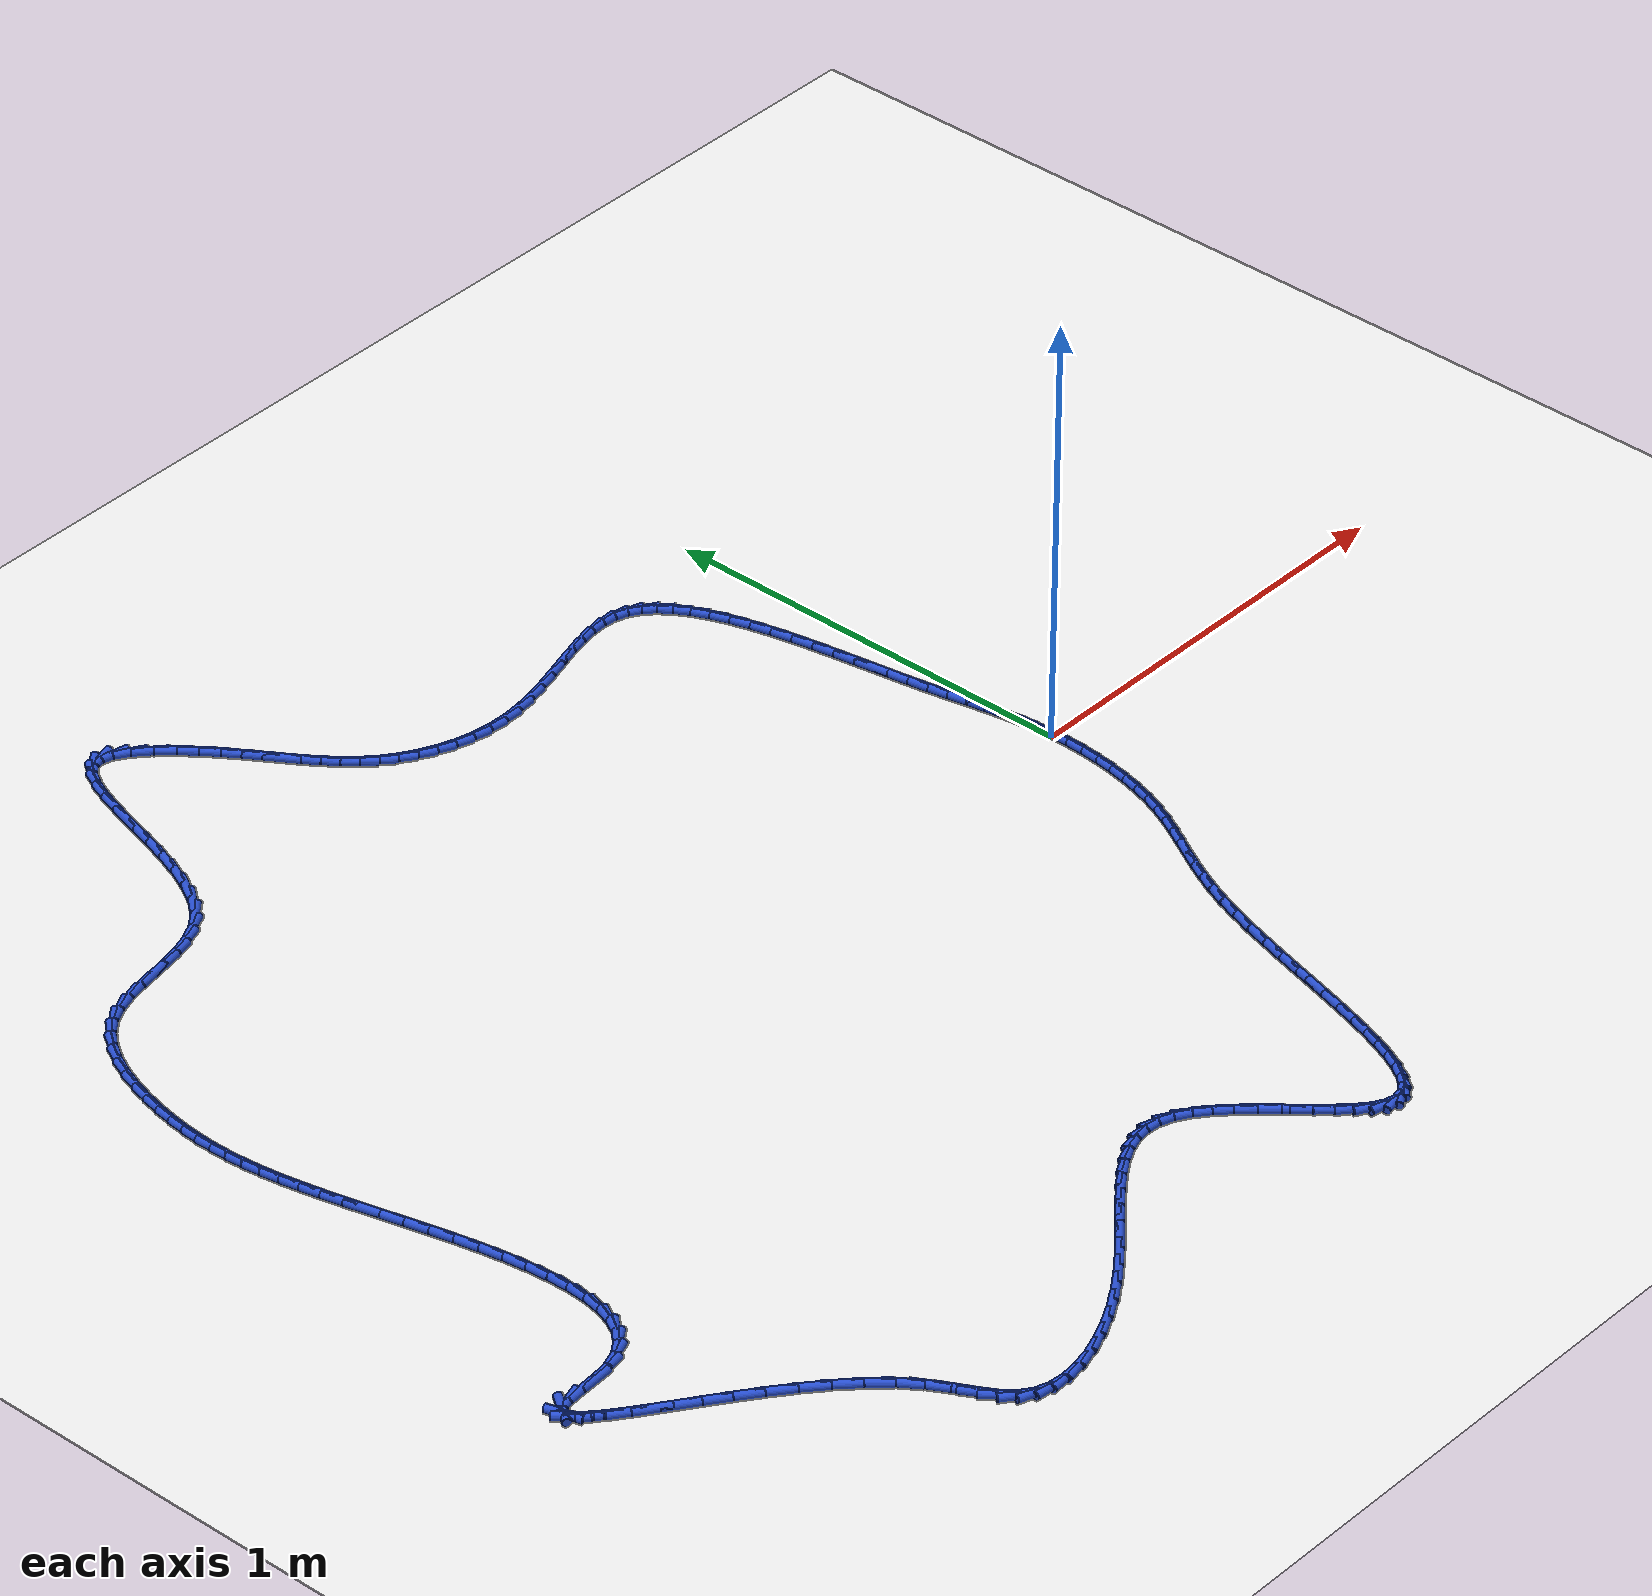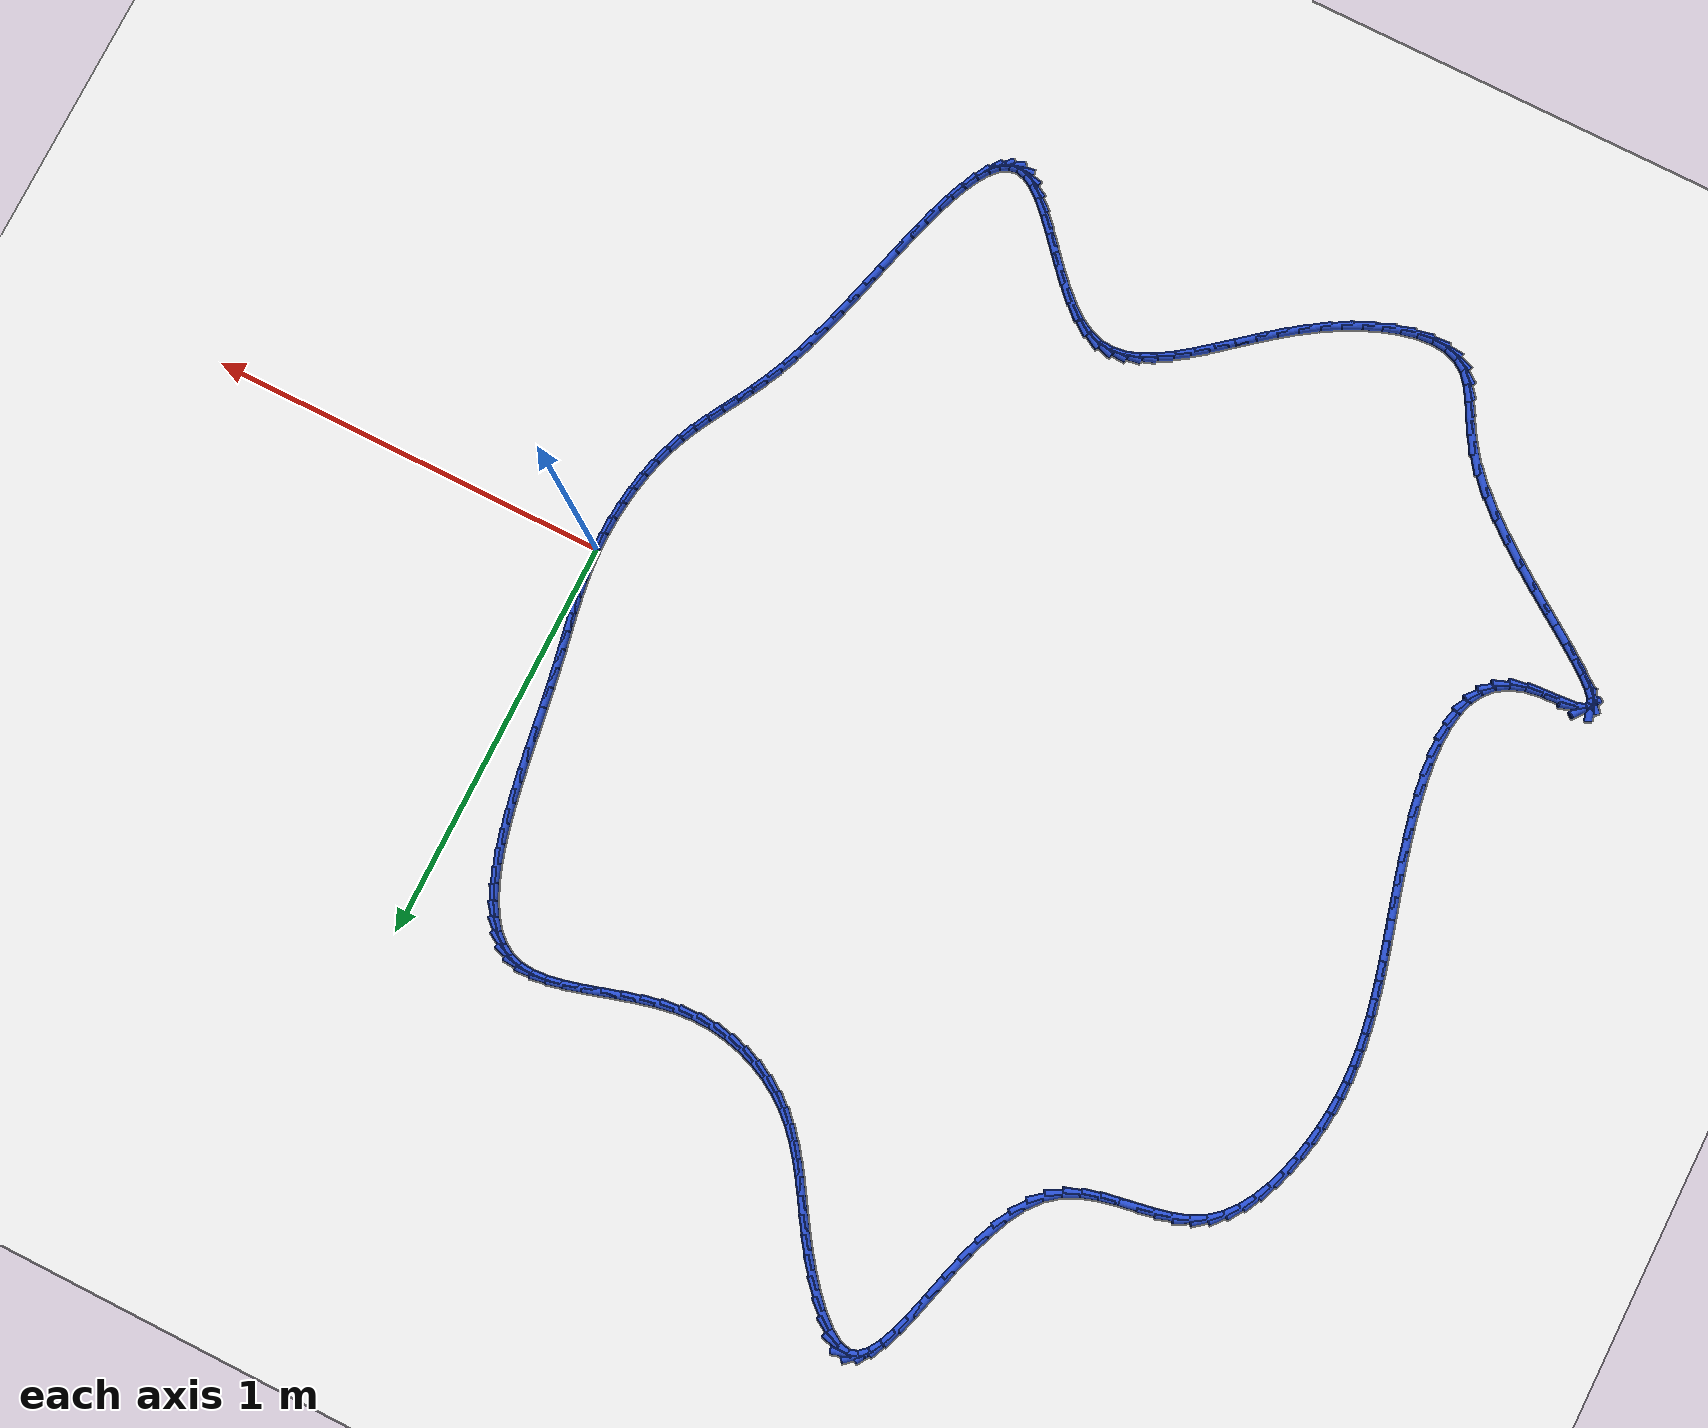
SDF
<sdf version="1.6">
 <world name="default">
  <light name="sun" type="directional">
   <pose>0 0 10 0 -0 0</pose>
   <diffuse>0.8 0.8 0.8 1</diffuse>
   <specular>0.2 0.2 0.2 1</specular>
   <attenuation>
    <range>1000</range>
    <constant>0.9</constant>
    <linear>0.01</linear>
    <quadratic>0.001</quadratic>
   </attenuation>
   <direction>-0.5 0.1 -0.9</direction>
  </light>
  <model name="ground_plane">
   <static>1</static>
   <link name="link">
    <collision name="collision">
     <geometry><plane><normal>0 0 1</normal><size>100 100</size></plane></geometry>
     <surface><friction><ode><mu>100</mu><mu2>50</mu2></ode></friction></surface>
    </collision>
    <visual name="visual">
     <cast_shadows>0</cast_shadows>
     <geometry><plane><normal>0 0 1</normal><size>100 100</size></plane></geometry>
     <material>
      <script><uri>file://media/materials/scripts/gazebo.material</uri><name>Gazebo/WhiteGlow</name></script>
     </material>
    </visual>
   </link>
  </model>
  <gravity>0 0 -9.8</gravity>
  <magnetic_field>6e-06 2.3e-05 -4.2e-05</magnetic_field>
  <atmosphere type="adiabatic"/>
  <physics name="default_physics" default="0" type="ode">
   <max_step_size>0.001</max_step_size>
   <real_time_factor>1</real_time_factor>
   <real_time_update_rate>1000</real_time_update_rate>
  </physics>
  <scene><ambient>0.4 0.4 0.4 1</ambient><background>0.7 0.7 0.7 1</background><shadows>1</shadows></scene>
  <spherical_coordinates>
   <surface_model>EARTH_WGS84</surface_model>
   <latitude_deg>0</latitude_deg>
   <longitude_deg>0</longitude_deg>
   <elevation>0</elevation>
   <heading_deg>0</heading_deg>
  </spherical_coordinates>
  <model name="line">
   <link name="link_0">
    <pose>-1.734723475976807e-17 1.3877787807814457e-17 0.01 0 1.57 -1.5043519604034143</pose>
    <collision name="collision">
     <geometry><cylinder><radius>0.01</radius><length>0.08</length></cylinder></geometry>
    </collision>
    <visual name="visual">
     <material>
      <script><name>Gazebo/Blue</name><uri>file://media/materials/scripts/gazebo.material</uri></script>
     </material>
     <geometry><cylinder><radius>0.01</radius><length>0.08</length></cylinder></geometry>
    </visual>
   </link>
   <link name="link_1">
    <pose>-0.0026834916813015803 0.04032759418932018 0.01 0 1.57 -1.458504746673012</pose>
    <collision name="collision">
     <geometry><cylinder><radius>0.01</radius><length>0.08</length></cylinder></geometry>
    </collision>
    <visual name="visual">
     <material>
      <script><name>Gazebo/Blue</name><uri>file://media/materials/scripts/gazebo.material</uri></script>
     </material>
     <geometry><cylinder><radius>0.01</radius><length>0.08</length></cylinder></geometry>
    </visual>
   </link>
   <link name="link_2">
    <pose>-0.007159424009895546 0.08001982713552917 0.01 0 1.57 -1.4218654142681841</pose>
    <collision name="collision">
     <geometry><cylinder><radius>0.01</radius><length>0.08</length></cylinder></geometry>
    </collision>
    <visual name="visual">
     <material>
      <script><name>Gazebo/Blue</name><uri>file://media/materials/scripts/gazebo.material</uri></script>
     </material>
     <geometry><cylinder><radius>0.01</radius><length>0.08</length></cylinder></geometry>
    </visual>
   </link>
   <link name="link_3">
    <pose>-0.013086417790616197 0.1195220881624992 0.01 0 1.57 -1.3956213127764878</pose>
    <collision name="collision">
     <geometry><cylinder><radius>0.01</radius><length>0.08</length></cylinder></geometry>
    </collision>
    <visual name="visual">
     <material>
      <script><name>Gazebo/Blue</name><uri>file://media/materials/scripts/gazebo.material</uri></script>
     </material>
     <geometry><cylinder><radius>0.01</radius><length>0.08</length></cylinder></geometry>
    </visual>
   </link>
   <link name="link_4">
    <pose>-0.02012309382829782 0.15927976659410242 0.01 0 1.57 -1.3802241135491946</pose>
    <collision name="collision">
     <geometry><cylinder><radius>0.01</radius><length>0.08</length></cylinder></geometry>
    </collision>
    <visual name="visual">
     <material>
      <script><name>Gazebo/Blue</name><uri>file://media/materials/scripts/gazebo.material</uri></script>
     </material>
     <geometry><cylinder><radius>0.01</radius><length>0.08</length></cylinder></geometry>
    </visual>
   </link>
   <link name="link_5">
    <pose>-0.027928072927774696 0.19973825175421117 0.01 0 1.57 -1.3754592863642896</pose>
    <collision name="collision">
     <geometry><cylinder><radius>0.01</radius><length>0.08</length></cylinder></geometry>
    </collision>
    <visual name="visual">
     <material>
      <script><name>Gazebo/Blue</name><uri>file://media/materials/scripts/gazebo.material</uri></script>
     </material>
     <geometry><cylinder><radius>0.01</radius><length>0.08</length></cylinder></geometry>
    </visual>
   </link>
   <link name="link_6">
    <pose>-0.03615997589388112 0.2413429329666976 0.01 0 1.57 -1.3805742379604398</pose>
    <collision name="collision">
     <geometry><cylinder><radius>0.01</radius><length>0.08</length></cylinder></geometry>
    </collision>
    <visual name="visual">
     <material>
      <script><name>Gazebo/Blue</name><uri>file://media/materials/scripts/gazebo.material</uri></script>
     </material>
     <geometry><cylinder><radius>0.01</radius><length>0.08</length></cylinder></geometry>
    </visual>
   </link>
   <link name="link_7">
    <pose>-0.04447742353145137 0.28453919955543405 0.01 0 1.57 -1.394176663468916</pose>
    <collision name="collision">
     <geometry><cylinder><radius>0.01</radius><length>0.08</length></cylinder></geometry>
    </collision>
    <visual name="visual">
     <material>
      <script><name>Gazebo/Blue</name><uri>file://media/materials/scripts/gazebo.material</uri></script>
     </material>
     <geometry><cylinder><radius>0.01</radius><length>0.08</length></cylinder></geometry>
    </visual>
   </link>
   <link name="link_8">
    <pose>-0.05254782357955602 0.32975674487690937 0.01 0 1.57 -1.4081775667946435</pose>
    <collision name="collision">
     <geometry><cylinder><radius>0.01</radius><length>0.08</length></cylinder></geometry>
    </collision>
    <visual name="visual">
     <material>
      <script><name>Gazebo/Blue</name><uri>file://media/materials/scripts/gazebo.material</uri></script>
     </material>
     <geometry><cylinder><radius>0.01</radius><length>0.08</length></cylinder></geometry>
    </visual>
   </link>
   <link name="link_9">
    <pose>-0.06029386538016309 0.37696925663138847 0.01 0 1.57 -1.4152116685557234</pose>
    <collision name="collision">
     <geometry><cylinder><radius>0.01</radius><length>0.08</length></cylinder></geometry>
    </collision>
    <visual name="visual">
     <material>
      <script><name>Gazebo/Blue</name><uri>file://media/materials/scripts/gazebo.material</uri></script>
     </material>
     <geometry><cylinder><radius>0.01</radius><length>0.08</length></cylinder></geometry>
    </visual>
   </link>
   <link name="link_10">
    <pose>-0.06792710896623179 0.42563441718418826 0.01 0 1.57 -1.4156871256024404</pose>
    <collision name="collision">
     <geometry><cylinder><radius>0.01</radius><length>0.08</length></cylinder></geometry>
    </collision>
    <visual name="visual">
     <material>
      <script><name>Gazebo/Blue</name><uri>file://media/materials/scripts/gazebo.material</uri></script>
     </material>
     <geometry><cylinder><radius>0.01</radius><length>0.08</length></cylinder></geometry>
    </visual>
   </link>
   <link name="link_11">
    <pose>-0.07567465131681447 0.475182155489417 0.01 0 1.57 -1.4099653269743906</pose>
    <collision name="collision">
     <geometry><cylinder><radius>0.01</radius><length>0.08</length></cylinder></geometry>
    </collision>
    <visual name="visual">
     <material>
      <script><name>Gazebo/Blue</name><uri>file://media/materials/scripts/gazebo.material</uri></script>
     </material>
     <geometry><cylinder><radius>0.01</radius><length>0.08</length></cylinder></geometry>
    </visual>
   </link>
   <link name="link_12">
    <pose>-0.08376358941096355 0.525042400501184 0.01 0 1.57 -1.3980013513036647</pose>
    <collision name="collision">
     <geometry><cylinder><radius>0.01</radius><length>0.08</length></cylinder></geometry>
    </collision>
    <visual name="visual">
     <material>
      <script><name>Gazebo/Blue</name><uri>file://media/materials/scripts/gazebo.material</uri></script>
     </material>
     <geometry><cylinder><radius>0.01</radius><length>0.08</length></cylinder></geometry>
    </visual>
   </link>
   <link name="link_13">
    <pose>-0.09242102022773138 0.5746450811735981 0.01 0 1.57 -1.3793611161459607</pose>
    <collision name="collision">
     <geometry><cylinder><radius>0.01</radius><length>0.08</length></cylinder></geometry>
    </collision>
    <visual name="visual">
     <material>
      <script><name>Gazebo/Blue</name><uri>file://media/materials/scripts/gazebo.material</uri></script>
     </material>
     <geometry><cylinder><radius>0.01</radius><length>0.08</length></cylinder></geometry>
    </visual>
   </link>
   <link name="link_14">
    <pose>-0.10187404074617036 0.623420126460768 0.01 0 1.57 -1.3531854236751217</pose>
    <collision name="collision">
     <geometry><cylinder><radius>0.01</radius><length>0.08</length></cylinder></geometry>
    </collision>
    <visual name="visual">
     <material>
      <script><name>Gazebo/Blue</name><uri>file://media/materials/scripts/gazebo.material</uri></script>
     </material>
     <geometry><cylinder><radius>0.01</radius><length>0.08</length></cylinder></geometry>
    </visual>
   </link>
   <link name="link_15">
    <pose>-0.11234974794533283 0.6707974653168023 0.01 0 1.57 -1.3180997096604181</pose>
    <collision name="collision">
     <geometry><cylinder><radius>0.01</radius><length>0.08</length></cylinder></geometry>
    </collision>
    <visual name="visual">
     <material>
      <script><name>Gazebo/Blue</name><uri>file://media/materials/scripts/gazebo.material</uri></script>
     </material>
     <geometry><cylinder><radius>0.01</radius><length>0.08</length></cylinder></geometry>
    </visual>
   </link>
   <link name="link_16">
    <pose>-0.12407523880427127 0.7162070266958106 0.01 0 1.57 -1.2720614204648206</pose>
    <collision name="collision">
     <geometry><cylinder><radius>0.01</radius><length>0.08</length></cylinder></geometry>
    </collision>
    <visual name="visual">
     <material>
      <script><name>Gazebo/Blue</name><uri>file://media/materials/scripts/gazebo.material</uri></script>
     </material>
     <geometry><cylinder><radius>0.01</radius><length>0.08</length></cylinder></geometry>
    </visual>
   </link>
   <link name="link_17">
    <pose>-0.137277610302038 0.7590787395519011 0.01 0 1.57 -1.212137518840905</pose>
    <collision name="collision">
     <geometry><cylinder><radius>0.01</radius><length>0.08</length></cylinder></geometry>
    </collision>
    <visual name="visual">
     <material>
      <script><name>Gazebo/Blue</name><uri>file://media/materials/scripts/gazebo.material</uri></script>
     </material>
     <geometry><cylinder><radius>0.01</radius><length>0.08</length></cylinder></geometry>
    </visual>
   </link>
   <link name="link_18">
    <pose>-0.15218395941768537 0.7988425328391827 0.01 0 1.57 -1.1342287332083532</pose>
    <collision name="collision">
     <geometry><cylinder><radius>0.01</radius><length>0.08</length></cylinder></geometry>
    </collision>
    <visual name="visual">
     <material>
      <script><name>Gazebo/Blue</name><uri>file://media/materials/scripts/gazebo.material</uri></script>
     </material>
     <geometry><cylinder><radius>0.01</radius><length>0.08</length></cylinder></geometry>
    </visual>
   </link>
   <link name="link_19">
    <pose>-0.16902138313026588 0.8349283355117649 0.01 0 1.57 -1.0328528033202082</pose>
    <collision name="collision">
     <geometry><cylinder><radius>0.01</radius><length>0.08</length></cylinder></geometry>
    </collision>
    <visual name="visual">
     <material>
      <script><name>Gazebo/Blue</name><uri>file://media/materials/scripts/gazebo.material</uri></script>
     </material>
     <geometry><cylinder><radius>0.01</radius><length>0.08</length></cylinder></geometry>
    </visual>
   </link>
   <link name="link_20">
    <pose>-0.18801697841883183 0.8667660765237559 0.01 0 1.57 -0.9013771820219533</pose>
    <collision name="collision">
     <geometry><cylinder><radius>0.01</radius><length>0.08</length></cylinder></geometry>
    </collision>
    <visual name="visual">
     <material>
      <script><name>Gazebo/Blue</name><uri>file://media/materials/scripts/gazebo.material</uri></script>
     </material>
     <geometry><cylinder><radius>0.01</radius><length>0.08</length></cylinder></geometry>
    </visual>
   </link>
   <link name="link_21">
    <pose>-0.20939784226243557 0.893785684829265 0.01 0 1.57 -0.7336778909110361</pose>
    <collision name="collision">
     <geometry><cylinder><radius>0.01</radius><length>0.08</length></cylinder></geometry>
    </collision>
    <visual name="visual">
     <material>
      <script><name>Gazebo/Blue</name><uri>file://media/materials/scripts/gazebo.material</uri></script>
     </material>
     <geometry><cylinder><radius>0.01</radius><length>0.08</length></cylinder></geometry>
    </visual>
   </link>
   <link name="link_22">
    <pose>-0.23339107164012962 0.9154170893824007 0.01 0 1.57 -0.5286505692719687</pose>
    <collision name="collision">
     <geometry><cylinder><radius>0.01</radius><length>0.08</length></cylinder></geometry>
    </collision>
    <visual name="visual">
     <material>
      <script><name>Gazebo/Blue</name><uri>file://media/materials/scripts/gazebo.material</uri></script>
     </material>
     <geometry><cylinder><radius>0.01</radius><length>0.08</length></cylinder></geometry>
    </visual>
   </link>
   <link name="link_23">
    <pose>-0.2602237635309661 0.9310902191372717 0.01 0 1.57 -0.2969897905777262</pose>
    <collision name="collision">
     <geometry><cylinder><radius>0.01</radius><length>0.08</length></cylinder></geometry>
    </collision>
    <visual name="visual">
     <material>
      <script><name>Gazebo/Blue</name><uri>file://media/materials/scripts/gazebo.material</uri></script>
     </material>
     <geometry><cylinder><radius>0.01</radius><length>0.08</length></cylinder></geometry>
    </visual>
   </link>
   <link name="link_24">
    <pose>-0.2901212865891916 0.9402400886339856 0.01 0 1.57 -0.07936995274728521</pose>
    <collision name="collision">
     <geometry><cylinder><radius>0.01</radius><length>0.08</length></cylinder></geometry>
    </collision>
    <visual name="visual">
     <material>
      <script><name>Gazebo/Blue</name><uri>file://media/materials/scripts/gazebo.material</uri></script>
     </material>
     <geometry><cylinder><radius>0.01</radius><length>0.08</length></cylinder></geometry>
    </visual>
   </link>
   <link name="link_25">
    <pose>-0.323117737645268 0.9428645286758671 0.01 0 1.57 0.07915999708260504</pose>
    <collision name="collision">
     <geometry><cylinder><radius>0.01</radius><length>0.08</length></cylinder></geometry>
    </collision>
    <visual name="visual">
     <material>
      <script><name>Gazebo/Blue</name><uri>file://media/materials/scripts/gazebo.material</uri></script>
     </material>
     <geometry><cylinder><radius>0.01</radius><length>0.08</length></cylinder></geometry>
    </visual>
   </link>
   <link name="link_26">
    <pose>-0.35888497132907304 0.9400272656993673 0.01 0 1.57 0.18432782117440763</pose>
    <collision name="collision">
     <geometry><cylinder><radius>0.01</radius><length>0.08</length></cylinder></geometry>
    </collision>
    <visual name="visual">
     <material>
      <script><name>Gazebo/Blue</name><uri>file://media/materials/scripts/gazebo.material</uri></script>
     </material>
     <geometry><cylinder><radius>0.01</radius><length>0.08</length></cylinder></geometry>
    </visual>
   </link>
   <link name="link_27">
    <pose>-0.39705448364341567 0.9329107811735707 0.01 0 1.57 0.24877695659034246</pose>
    <collision name="collision">
     <geometry><cylinder><radius>0.01</radius><length>0.08</length></cylinder></geometry>
    </collision>
    <visual name="visual">
     <material>
      <script><name>Gazebo/Blue</name><uri>file://media/materials/scripts/gazebo.material</uri></script>
     </material>
     <geometry><cylinder><radius>0.01</radius><length>0.08</length></cylinder></geometry>
    </visual>
   </link>
   <link name="link_28">
    <pose>-0.4372577705911052 0.9226975565675611 0.01 0 1.57 0.2819401736774933</pose>
    <collision name="collision">
     <geometry><cylinder><radius>0.01</radius><length>0.08</length></cylinder></geometry>
    </collision>
    <visual name="visual">
     <material>
      <script><name>Gazebo/Blue</name><uri>file://media/materials/scripts/gazebo.material</uri></script>
     </material>
     <geometry><cylinder><radius>0.01</radius><length>0.08</length></cylinder></geometry>
    </visual>
   </link>
   <link name="link_29">
    <pose>-0.4791263281749508 0.9105700733504232 0.01 0 1.57 0.2895356792802546</pose>
    <collision name="collision">
     <geometry><cylinder><radius>0.01</radius><length>0.08</length></cylinder></geometry>
    </collision>
    <visual name="visual">
     <material>
      <script><name>Gazebo/Blue</name><uri>file://media/materials/scripts/gazebo.material</uri></script>
     </material>
     <geometry><cylinder><radius>0.01</radius><length>0.08</length></cylinder></geometry>
    </visual>
   </link>
   <link name="link_30">
    <pose>-0.5222916523977619 0.897710812991241 0.01 0 1.57 0.27431949389599986</pose>
    <collision name="collision">
     <geometry><cylinder><radius>0.01</radius><length>0.08</length></cylinder></geometry>
    </collision>
    <visual name="visual">
     <material>
      <script><name>Gazebo/Blue</name><uri>file://media/materials/scripts/gazebo.material</uri></script>
     </material>
     <geometry><cylinder><radius>0.01</radius><length>0.08</length></cylinder></geometry>
    </visual>
   </link>
   <link name="link_31">
    <pose>-0.5663852392623479 0.8853022569590989 0.01 0 1.57 0.23678477718743685</pose>
    <collision name="collision">
     <geometry><cylinder><radius>0.01</radius><length>0.08</length></cylinder></geometry>
    </collision>
    <visual name="visual">
     <material>
      <script><name>Gazebo/Blue</name><uri>file://media/materials/scripts/gazebo.material</uri></script>
     </material>
     <geometry><cylinder><radius>0.01</radius><length>0.08</length></cylinder></geometry>
    </visual>
   </link>
   <link name="link_32">
    <pose>-0.6110385847715172 0.8745268867230808 0.01 0 1.57 0.17566572827166452</pose>
    <collision name="collision">
     <geometry><cylinder><radius>0.01</radius><length>0.08</length></cylinder></geometry>
    </collision>
    <visual name="visual">
     <material>
      <script><name>Gazebo/Blue</name><uri>file://media/materials/scripts/gazebo.material</uri></script>
     </material>
     <geometry><cylinder><radius>0.01</radius><length>0.08</length></cylinder></geometry>
    </visual>
   </link>
   <link name="link_33">
    <pose>-0.6558831849280798 0.8665671837522715 0.01 0 1.57 0.08845871000474242</pose>
    <collision name="collision">
     <geometry><cylinder><radius>0.01</radius><length>0.08</length></cylinder></geometry>
    </collision>
    <visual name="visual">
     <material>
      <script><name>Gazebo/Blue</name><uri>file://media/materials/scripts/gazebo.material</uri></script>
     </material>
     <geometry><cylinder><radius>0.01</radius><length>0.08</length></cylinder></geometry>
    </visual>
   </link>
   <link name="link_34">
    <pose>-0.7005505357237408 0.8626056291470503 0.01 0 1.57 -0.021541568695381017</pose>
    <collision name="collision">
     <geometry><cylinder><radius>0.01</radius><length>0.08</length></cylinder></geometry>
    </collision>
    <visual name="visual">
     <material>
      <script><name>Gazebo/Blue</name><uri>file://media/materials/scripts/gazebo.material</uri></script>
     </material>
     <geometry><cylinder><radius>0.01</radius><length>0.08</length></cylinder></geometry>
    </visual>
   </link>
   <link name="link_35">
    <pose>-0.7446640423481244 0.8635560502958258 0.01 0 1.57 -0.1321794380489603</pose>
    <collision name="collision">
     <geometry><cylinder><radius>0.01</radius><length>0.08</length></cylinder></geometry>
    </collision>
    <visual name="visual">
     <material>
      <script><name>Gazebo/Blue</name><uri>file://media/materials/scripts/gazebo.material</uri></script>
     </material>
     <geometry><cylinder><radius>0.01</radius><length>0.08</length></cylinder></geometry>
    </visual>
   </link>
   <link name="link_36">
    <pose>-0.7878158195082968 0.8692932794163742 0.01 0 1.57 -0.23830064526157757</pose>
    <collision name="collision">
     <geometry><cylinder><radius>0.01</radius><length>0.08</length></cylinder></geometry>
    </collision>
    <visual name="visual">
     <material>
      <script><name>Gazebo/Blue</name><uri>file://media/materials/scripts/gazebo.material</uri></script>
     </material>
     <geometry><cylinder><radius>0.01</radius><length>0.08</length></cylinder></geometry>
    </visual>
   </link>
   <link name="link_37">
    <pose>-0.8295904186403948 0.8794410115969616 0.01 0 1.57 -0.3408629632215356</pose>
    <collision name="collision">
     <geometry><cylinder><radius>0.01</radius><length>0.08</length></cylinder></geometry>
    </collision>
    <visual name="visual">
     <material>
      <script><name>Gazebo/Blue</name><uri>file://media/materials/scripts/gazebo.material</uri></script>
     </material>
     <geometry><cylinder><radius>0.01</radius><length>0.08</length></cylinder></geometry>
    </visual>
   </link>
   <link name="link_38">
    <pose>-0.8695723911805537 0.8936229419258521 0.01 0 1.57 -0.44122601465009215</pose>
    <collision name="collision">
     <geometry><cylinder><radius>0.01</radius><length>0.08</length></cylinder></geometry>
    </collision>
    <visual name="visual">
     <material>
      <script><name>Gazebo/Blue</name><uri>file://media/materials/scripts/gazebo.material</uri></script>
     </material>
     <geometry><cylinder><radius>0.01</radius><length>0.08</length></cylinder></geometry>
    </visual>
   </link>
   <link name="link_39">
    <pose>-0.9073462885649108 0.9114627654913123 0.01 0 1.57 -0.5410716455367891</pose>
    <collision name="collision">
     <geometry><cylinder><radius>0.01</radius><length>0.08</length></cylinder></geometry>
    </collision>
    <visual name="visual">
     <material>
      <script><name>Gazebo/Blue</name><uri>file://media/materials/scripts/gazebo.material</uri></script>
     </material>
     <geometry><cylinder><radius>0.01</radius><length>0.08</length></cylinder></geometry>
    </visual>
   </link>
   <link name="link_40">
    <pose>-0.9424966622296017 0.9325841773816068 0.01 0 1.57 -0.6423642866143113</pose>
    <collision name="collision">
     <geometry><cylinder><radius>0.01</radius><length>0.08</length></cylinder></geometry>
    </collision>
    <visual name="visual">
     <material>
      <script><name>Gazebo/Blue</name><uri>file://media/materials/scripts/gazebo.material</uri></script>
     </material>
     <geometry><cylinder><radius>0.01</radius><length>0.08</length></cylinder></geometry>
    </visual>
   </link>
   <link name="link_41">
    <pose>-0.9746082651095567 0.956610888760878 0.01 0 1.57 -0.743422803803684</pose>
    <collision name="collision">
     <geometry><cylinder><radius>0.01</radius><length>0.08</length></cylinder></geometry>
    </collision>
    <visual name="visual">
     <material>
      <script><name>Gazebo/Blue</name><uri>file://media/materials/scripts/gazebo.material</uri></script>
     </material>
     <geometry><cylinder><radius>0.01</radius><length>0.08</length></cylinder></geometry>
    </visual>
   </link>
   <link name="link_42">
    <pose>-1.0035139991393027 0.9831864084936581 0.01 0 1.57 -0.8318706769109073</pose>
    <collision name="collision">
     <geometry><cylinder><radius>0.01</radius><length>0.08</length></cylinder></geometry>
    </collision>
    <visual name="visual">
     <material>
      <script><name>Gazebo/Blue</name><uri>file://media/materials/scripts/gazebo.material</uri></script>
     </material>
     <geometry><cylinder><radius>0.01</radius><length>0.08</length></cylinder></geometry>
    </visual>
   </link>
   <link name="link_43">
    <pose>-1.0297781559851649 1.0120125968172542 0.01 0 1.57 -0.9022364067525769</pose>
    <collision name="collision">
     <geometry><cylinder><radius>0.01</radius><length>0.08</length></cylinder></geometry>
    </collision>
    <visual name="visual">
     <material>
      <script><name>Gazebo/Blue</name><uri>file://media/materials/scripts/gazebo.material</uri></script>
     </material>
     <geometry><cylinder><radius>0.01</radius><length>0.08</length></cylinder></geometry>
    </visual>
   </link>
   <link name="link_44">
    <pose>-1.054099110921042 1.0428020113608394 0.01 0 1.57 -0.9528615131294401</pose>
    <collision name="collision">
     <geometry><cylinder><radius>0.01</radius><length>0.08</length></cylinder></geometry>
    </collision>
    <visual name="visual">
     <material>
      <script><name>Gazebo/Blue</name><uri>file://media/materials/scripts/gazebo.material</uri></script>
     </material>
     <geometry><cylinder><radius>0.01</radius><length>0.08</length></cylinder></geometry>
    </visual>
   </link>
   <link name="link_45">
    <pose>-1.0771752392208316 1.0752672097535865 0.01 0 1.57 -0.9835988584621633</pose>
    <collision name="collision">
     <geometry><cylinder><radius>0.01</radius><length>0.08</length></cylinder></geometry>
    </collision>
    <visual name="visual">
     <material>
      <script><name>Gazebo/Blue</name><uri>file://media/materials/scripts/gazebo.material</uri></script>
     </material>
     <geometry><cylinder><radius>0.01</radius><length>0.08</length></cylinder></geometry>
    </visual>
   </link>
   <link name="link_46">
    <pose>-1.0997049161584325 1.1091207496246687 0.01 0 1.57 -0.9952015175900911</pose>
    <collision name="collision">
     <geometry><cylinder><radius>0.01</radius><length>0.08</length></cylinder></geometry>
    </collision>
    <visual name="visual">
     <material>
      <script><name>Gazebo/Blue</name><uri>file://media/materials/scripts/gazebo.material</uri></script>
     </material>
     <geometry><cylinder><radius>0.01</radius><length>0.08</length></cylinder></geometry>
    </visual>
   </link>
   <link name="link_47">
    <pose>-1.1223865170077425 1.1440751886032592 0.01 0 1.57 -0.9888836047444356</pose>
    <collision name="collision">
     <geometry><cylinder><radius>0.01</radius><length>0.08</length></cylinder></geometry>
    </collision>
    <visual name="visual">
     <material>
      <script><name>Gazebo/Blue</name><uri>file://media/materials/scripts/gazebo.material</uri></script>
     </material>
     <geometry><cylinder><radius>0.01</radius><length>0.08</length></cylinder></geometry>
    </visual>
   </link>
   <link name="link_48">
    <pose>-1.1459184170426593 1.1798430843185308 0.01 0 1.57 -0.9661085560042411</pose>
    <collision name="collision">
     <geometry><cylinder><radius>0.01</radius><length>0.08</length></cylinder></geometry>
    </collision>
    <visual name="visual">
     <material>
      <script><name>Gazebo/Blue</name><uri>file://media/materials/scripts/gazebo.material</uri></script>
     </material>
     <geometry><cylinder><radius>0.01</radius><length>0.08</length></cylinder></geometry>
    </visual>
   </link>
   <link name="link_49">
    <pose>-1.1709989915370824 1.2161369943996574 0.01 0 1.57 -0.9285531446263314</pose>
    <collision name="collision">
     <geometry><cylinder><radius>0.01</radius><length>0.08</length></cylinder></geometry>
    </collision>
    <visual name="visual">
     <material>
      <script><name>Gazebo/Blue</name><uri>file://media/materials/scripts/gazebo.material</uri></script>
     </material>
     <geometry><cylinder><radius>0.01</radius><length>0.08</length></cylinder></geometry>
    </visual>
   </link>
   <link name="link_50">
    <pose>-1.198326615764909 1.2526694764758117 0.01 0 1.57 -0.8781080014655945</pose>
    <collision name="collision">
     <geometry><cylinder><radius>0.01</radius><length>0.08</length></cylinder></geometry>
    </collision>
    <visual name="visual">
     <material>
      <script><name>Gazebo/Blue</name><uri>file://media/materials/scripts/gazebo.material</uri></script>
     </material>
     <geometry><cylinder><radius>0.01</radius><length>0.08</length></cylinder></geometry>
    </visual>
   </link>
   <link name="link_51">
    <pose>-1.22851689410118 1.2890491912320328 0.01 0 1.57 -0.8127220401557662</pose>
    <collision name="collision">
     <geometry><cylinder><radius>0.01</radius><length>0.08</length></cylinder></geometry>
    </collision>
    <visual name="visual">
     <material>
      <script><name>Gazebo/Blue</name><uri>file://media/materials/scripts/gazebo.material</uri></script>
     </material>
     <geometry><cylinder><radius>0.01</radius><length>0.08</length></cylinder></geometry>
    </visual>
   </link>
   <link name="link_52">
    <pose>-1.260803827052172 1.3231505615723282 0.01 0 1.57 -0.7161709486386947</pose>
    <collision name="collision">
     <geometry><cylinder><radius>0.01</radius><length>0.08</length></cylinder></geometry>
    </collision>
    <visual name="visual">
     <material>
      <script><name>Gazebo/Blue</name><uri>file://media/materials/scripts/gazebo.material</uri></script>
     </material>
     <geometry><cylinder><radius>0.01</radius><length>0.08</length></cylinder></geometry>
    </visual>
   </link>
   <link name="link_53">
    <pose>-1.2932795545349434 1.3514147068183548 0.01 0 1.57 -0.5497387924867193</pose>
    <collision name="collision">
     <geometry><cylinder><radius>0.01</radius><length>0.08</length></cylinder></geometry>
    </collision>
    <visual name="visual">
     <material>
      <script><name>Gazebo/Blue</name><uri>file://media/materials/scripts/gazebo.material</uri></script>
     </material>
     <geometry><cylinder><radius>0.01</radius><length>0.08</length></cylinder></geometry>
    </visual>
   </link>
   <link name="link_54">
    <pose>-1.3240019408494101 1.3702397223313105 0.01 0 1.57 -0.21931060222069204</pose>
    <collision name="collision">
     <geometry><cylinder><radius>0.01</radius><length>0.08</length></cylinder></geometry>
    </collision>
    <visual name="visual">
     <material>
      <script><name>Gazebo/Blue</name><uri>file://media/materials/scripts/gazebo.material</uri></script>
     </material>
     <geometry><cylinder><radius>0.01</radius><length>0.08</length></cylinder></geometry>
    </visual>
   </link>
   <link name="link_55">
    <pose>-1.351162445207441 1.3762936809147073 0.01 0 1.57 0.29207988981076444</pose>
    <collision name="collision">
     <geometry><cylinder><radius>0.01</radius><length>0.08</length></cylinder></geometry>
    </collision>
    <visual name="visual">
     <material>
      <script><name>Gazebo/Blue</name><uri>file://media/materials/scripts/gazebo.material</uri></script>
     </material>
     <geometry><cylinder><radius>0.01</radius><length>0.08</length></cylinder></geometry>
    </visual>
   </link>
   <link name="link_56">
    <pose>-1.374458936680389 1.3692889081432986 0.01 0 1.57 0.7425917595814879</pose>
    <collision name="collision">
     <geometry><cylinder><radius>0.01</radius><length>0.08</length></cylinder></geometry>
    </collision>
    <visual name="visual">
     <material>
      <script><name>Gazebo/Blue</name><uri>file://media/materials/scripts/gazebo.material</uri></script>
     </material>
     <geometry><cylinder><radius>0.01</radius><length>0.08</length></cylinder></geometry>
    </visual>
   </link>
   <link name="link_57">
    <pose>-1.394539468112577 1.35085792386423 0.01 0 1.57 1.0146006849666114</pose>
    <collision name="collision">
     <geometry><cylinder><radius>0.01</radius><length>0.08</length></cylinder></geometry>
    </collision>
    <visual name="visual">
     <material>
      <script><name>Gazebo/Blue</name><uri>file://media/materials/scripts/gazebo.material</uri></script>
     </material>
     <geometry><cylinder><radius>0.01</radius><length>0.08</length></cylinder></geometry>
    </visual>
   </link>
   <link name="link_58">
    <pose>-1.4120669820242775 1.3226633379675323 0.01 0 1.57 1.1639929975273127</pose>
    <collision name="collision">
     <geometry><cylinder><radius>0.01</radius><length>0.08</length></cylinder></geometry>
    </collision>
    <visual name="visual">
     <material>
      <script><name>Gazebo/Blue</name><uri>file://media/materials/scripts/gazebo.material</uri></script>
     </material>
     <geometry><cylinder><radius>0.01</radius><length>0.08</length></cylinder></geometry>
    </visual>
   </link>
   <link name="link_59">
    <pose>-1.4277044209357659 1.2863677603432375 0.01 0 1.57 1.2455610924468612</pose>
    <collision name="collision">
     <geometry><cylinder><radius>0.01</radius><length>0.08</length></cylinder></geometry>
    </collision>
    <visual name="visual">
     <material>
      <script><name>Gazebo/Blue</name><uri>file://media/materials/scripts/gazebo.material</uri></script>
     </material>
     <geometry><cylinder><radius>0.01</radius><length>0.08</length></cylinder></geometry>
    </visual>
   </link>
   <link name="link_60">
    <pose>-1.4421147273673145 1.2436338008813768 0.01 0 1.57 1.2872134475839898</pose>
    <collision name="collision">
     <geometry><cylinder><radius>0.01</radius><length>0.08</length></cylinder></geometry>
    </collision>
    <visual name="visual">
     <material>
      <script><name>Gazebo/Blue</name><uri>file://media/materials/scripts/gazebo.material</uri></script>
     </material>
     <geometry><cylinder><radius>0.01</radius><length>0.08</length></cylinder></geometry>
    </visual>
   </link>
   <link name="link_61">
    <pose>-1.4559608438391982 1.196124069471983 0.01 0 1.57 1.3019972420515635</pose>
    <collision name="collision">
     <geometry><cylinder><radius>0.01</radius><length>0.08</length></cylinder></geometry>
    </collision>
    <visual name="visual">
     <material>
      <script><name>Gazebo/Blue</name><uri>file://media/materials/scripts/gazebo.material</uri></script>
     </material>
     <geometry><cylinder><radius>0.01</radius><length>0.08</length></cylinder></geometry>
    </visual>
   </link>
   <link name="link_62">
    <pose>-1.4699057128716906 1.1455011760050868 0.01 0 1.57 1.2955452986261684</pose>
    <collision name="collision">
     <geometry><cylinder><radius>0.01</radius><length>0.08</length></cylinder></geometry>
    </collision>
    <visual name="visual">
     <material>
      <script><name>Gazebo/Blue</name><uri>file://media/materials/scripts/gazebo.material</uri></script>
     </material>
     <geometry><cylinder><radius>0.01</radius><length>0.08</length></cylinder></geometry>
    </visual>
   </link>
   <link name="link_63">
    <pose>-1.484612276985065 1.0934277303707205 0.01 0 1.57 1.2692379750336242</pose>
    <collision name="collision">
     <geometry><cylinder><radius>0.01</radius><length>0.08</length></cylinder></geometry>
    </collision>
    <visual name="visual">
     <material>
      <script><name>Gazebo/Blue</name><uri>file://media/materials/scripts/gazebo.material</uri></script>
     </material>
     <geometry><cylinder><radius>0.01</radius><length>0.08</length></cylinder></geometry>
    </visual>
   </link>
   <link name="link_64">
    <pose>-1.5007434786995952 1.0415663424589154 0.01 0 1.57 1.2212870905643312</pose>
    <collision name="collision">
     <geometry><cylinder><radius>0.01</radius><length>0.08</length></cylinder></geometry>
    </collision>
    <visual name="visual">
     <material>
      <script><name>Gazebo/Blue</name><uri>file://media/materials/scripts/gazebo.material</uri></script>
     </material>
     <geometry><cylinder><radius>0.01</radius><length>0.08</length></cylinder></geometry>
    </visual>
   </link>
   <link name="link_65">
    <pose>-1.5189622605355555 0.9915796221597035 0.01 0 1.57 1.1467425360948533</pose>
    <collision name="collision">
     <geometry><cylinder><radius>0.01</radius><length>0.08</length></cylinder></geometry>
    </collision>
    <visual name="visual">
     <material>
      <script><name>Gazebo/Blue</name><uri>file://media/materials/scripts/gazebo.material</uri></script>
     </material>
     <geometry><cylinder><radius>0.01</radius><length>0.08</length></cylinder></geometry>
    </visual>
   </link>
   <link name="link_66">
    <pose>-1.53993156501322 0.9451301793631166 0.01 0 1.57 1.0369438177246564</pose>
    <collision name="collision">
     <geometry><cylinder><radius>0.01</radius><length>0.08</length></cylinder></geometry>
    </collision>
    <visual name="visual">
     <material>
      <script><name>Gazebo/Blue</name><uri>file://media/materials/scripts/gazebo.material</uri></script>
     </material>
     <geometry><cylinder><radius>0.01</radius><length>0.08</length></cylinder></geometry>
    </visual>
   </link>
   <link name="link_67">
    <pose>-1.5643143346528616 0.9038806239591863 0.01 0 1.57 0.8794434792600202</pose>
    <collision name="collision">
     <geometry><cylinder><radius>0.01</radius><length>0.08</length></cylinder></geometry>
    </collision>
    <visual name="visual">
     <material>
      <script><name>Gazebo/Blue</name><uri>file://media/materials/scripts/gazebo.material</uri></script>
     </material>
     <geometry><cylinder><radius>0.01</radius><length>0.08</length></cylinder></geometry>
    </visual>
   </link>
   <link name="link_68">
    <pose>-1.592773511974754 0.869493565837944 0.01 0 1.57 0.6692314625230525</pose>
    <collision name="collision">
     <geometry><cylinder><radius>0.01</radius><length>0.08</length></cylinder></geometry>
    </collision>
    <visual name="visual">
     <material>
      <script><name>Gazebo/Blue</name><uri>file://media/materials/scripts/gazebo.material</uri></script>
     </material>
     <geometry><cylinder><radius>0.01</radius><length>0.08</length></cylinder></geometry>
    </visual>
   </link>
   <link name="link_69">
    <pose>-1.625829710944992 0.8433459798033992 0.01 0 1.57 0.46773969628238926</pose>
    <collision name="collision">
     <geometry><cylinder><radius>0.01</radius><length>0.08</length></cylinder></geometry>
    </collision>
    <visual name="visual">
     <material>
      <script><name>Gazebo/Blue</name><uri>file://media/materials/scripts/gazebo.material</uri></script>
     </material>
     <geometry><cylinder><radius>0.01</radius><length>0.08</length></cylinder></geometry>
    </visual>
   </link>
   <link name="link_70">
    <pose>-1.662908224545969 0.8246166724479618 0.01 0 1.57 0.3175477855886142</pose>
    <collision name="collision">
     <geometry><cylinder><radius>0.01</radius><length>0.08</length></cylinder></geometry>
    </collision>
    <visual name="visual">
     <material>
      <script><name>Gazebo/Blue</name><uri>file://media/materials/scripts/gazebo.material</uri></script>
     </material>
     <geometry><cylinder><radius>0.01</radius><length>0.08</length></cylinder></geometry>
    </visual>
   </link>
   <link name="link_71">
    <pose>-1.7029258974542574 0.8114640600677463 0.01 0 1.57 0.22136377452533826</pose>
    <collision name="collision">
     <geometry><cylinder><radius>0.01</radius><length>0.08</length></cylinder></geometry>
    </collision>
    <visual name="visual">
     <material>
      <script><name>Gazebo/Blue</name><uri>file://media/materials/scripts/gazebo.material</uri></script>
     </material>
     <geometry><cylinder><radius>0.01</radius><length>0.08</length></cylinder></geometry>
    </visual>
   </link>
   <link name="link_72">
    <pose>-1.7447967756332157 0.8020409423017258 0.01 0 1.57 0.1750462758483027</pose>
    <collision name="collision">
     <geometry><cylinder><radius>0.01</radius><length>0.08</length></cylinder></geometry>
    </collision>
    <visual name="visual">
     <material>
      <script><name>Gazebo/Blue</name><uri>file://media/materials/scripts/gazebo.material</uri></script>
     </material>
     <geometry><cylinder><radius>0.01</radius><length>0.08</length></cylinder></geometry>
    </visual>
   </link>
   <link name="link_73">
    <pose>-1.7874349050462008 0.794500118788874 0.01 0 1.57 0.1755336125361452</pose>
    <collision name="collision">
     <geometry><cylinder><radius>0.01</radius><length>0.08</length></cylinder></geometry>
    </collision>
    <visual name="visual">
     <material>
      <script><name>Gazebo/Blue</name><uri>file://media/materials/scripts/gazebo.material</uri></script>
     </material>
     <geometry><cylinder><radius>0.01</radius><length>0.08</length></cylinder></geometry>
    </visual>
   </link>
   <link name="link_74">
    <pose>-1.82975433165657 0.7869943891681641 0.01 0 1.57 0.22391870407483172</pose>
    <collision name="collision">
     <geometry><cylinder><radius>0.01</radius><length>0.08</length></cylinder></geometry>
    </collision>
    <visual name="visual">
     <material>
      <script><name>Gazebo/Blue</name><uri>file://media/materials/scripts/gazebo.material</uri></script>
     </material>
     <geometry><cylinder><radius>0.01</radius><length>0.08</length></cylinder></geometry>
    </visual>
   </link>
   <link name="link_75">
    <pose>-1.8706691014276802 0.7776765530785691 0.01 0 1.57 0.32570586607354196</pose>
    <collision name="collision">
     <geometry><cylinder><radius>0.01</radius><length>0.08</length></cylinder></geometry>
    </collision>
    <visual name="visual">
     <material>
      <script><name>Gazebo/Blue</name><uri>file://media/materials/scripts/gazebo.material</uri></script>
     </material>
     <geometry><cylinder><radius>0.01</radius><length>0.08</length></cylinder></geometry>
    </visual>
   </link>
   <link name="link_76">
    <pose>-1.9090932603228885 0.7646994101590626 0.01 0 1.57 0.48765469352245133</pose>
    <collision name="collision">
     <geometry><cylinder><radius>0.01</radius><length>0.08</length></cylinder></geometry>
    </collision>
    <visual name="visual">
     <material>
      <script><name>Gazebo/Blue</name><uri>file://media/materials/scripts/gazebo.material</uri></script>
     </material>
     <geometry><cylinder><radius>0.01</radius><length>0.08</length></cylinder></geometry>
    </visual>
   </link>
   <link name="link_77">
    <pose>-1.9439412997885903 0.7462167295690708 0.01 0 1.57 0.6888846750801644</pose>
    <collision name="collision">
     <geometry><cylinder><radius>0.01</radius><length>0.08</length></cylinder></geometry>
    </collision>
    <visual name="visual">
     <material>
      <script><name>Gazebo/Blue</name><uri>file://media/materials/scripts/gazebo.material</uri></script>
     </material>
     <geometry><cylinder><radius>0.01</radius><length>0.08</length></cylinder></geometry>
    </visual>
   </link>
   <link name="link_78">
    <pose>-1.974453420919056 0.721091133865743 0.01 0 1.57 0.8660433401253641</pose>
    <collision name="collision">
     <geometry><cylinder><radius>0.01</radius><length>0.08</length></cylinder></geometry>
    </collision>
    <visual name="visual">
     <material>
      <script><name>Gazebo/Blue</name><uri>file://media/materials/scripts/gazebo.material</uri></script>
     </material>
     <geometry><cylinder><radius>0.01</radius><length>0.08</length></cylinder></geometry>
    </visual>
   </link>
   <link name="link_79">
    <pose>-2.0007707052235726 0.6901458634365524 0.01 0 1.57 1.0088813632612788</pose>
    <collision name="collision">
     <geometry><cylinder><radius>0.01</radius><length>0.08</length></cylinder></geometry>
    </collision>
    <visual name="visual">
     <material>
      <script><name>Gazebo/Blue</name><uri>file://media/materials/scripts/gazebo.material</uri></script>
     </material>
     <geometry><cylinder><radius>0.01</radius><length>0.08</length></cylinder></geometry>
    </visual>
   </link>
   <link name="link_80">
    <pose>-2.023188690385943 0.6545403070907864 0.01 0 1.57 1.1223804548551266</pose>
    <collision name="collision">
     <geometry><cylinder><radius>0.01</radius><length>0.08</length></cylinder></geometry>
    </collision>
    <visual name="visual">
     <material>
      <script><name>Gazebo/Blue</name><uri>file://media/materials/scripts/gazebo.material</uri></script>
     </material>
     <geometry><cylinder><radius>0.01</radius><length>0.08</length></cylinder></geometry>
    </visual>
   </link>
   <link name="link_81">
    <pose>-2.042002914089967 0.6154338536377314 0.01 0 1.57 1.2128082125450559</pose>
    <collision name="collision">
     <geometry><cylinder><radius>0.01</radius><length>0.08</length></cylinder></geometry>
    </collision>
    <visual name="visual">
     <material>
      <script><name>Gazebo/Blue</name><uri>file://media/materials/scripts/gazebo.material</uri></script>
     </material>
     <geometry><cylinder><radius>0.01</radius><length>0.08</length></cylinder></geometry>
    </visual>
   </link>
   <link name="link_82">
    <pose>-2.057508914019447 0.5739858918866745 0.01 0 1.57 1.2857155305334727</pose>
    <collision name="collision">
     <geometry><cylinder><radius>0.01</radius><length>0.08</length></cylinder></geometry>
    </collision>
    <visual name="visual">
     <material>
      <script><name>Gazebo/Blue</name><uri>file://media/materials/scripts/gazebo.material</uri></script>
     </material>
     <geometry><cylinder><radius>0.01</radius><length>0.08</length></cylinder></geometry>
    </visual>
   </link>
   <link name="link_83">
    <pose>-2.070002227858182 0.5313558106469018 0.01 0 1.57 1.3454847382802289</pose>
    <collision name="collision">
     <geometry><cylinder><radius>0.01</radius><length>0.08</length></cylinder></geometry>
    </collision>
    <visual name="visual">
     <material>
      <script><name>Gazebo/Blue</name><uri>file://media/materials/scripts/gazebo.material</uri></script>
     </material>
     <geometry><cylinder><radius>0.01</radius><length>0.08</length></cylinder></geometry>
    </visual>
   </link>
   <link name="link_84">
    <pose>-2.0797783932899745 0.4887029987277014 0.01 0 1.57 1.3963062252807046</pose>
    <collision name="collision">
     <geometry><cylinder><radius>0.01</radius><length>0.08</length></cylinder></geometry>
    </collision>
    <visual name="visual">
     <material>
      <script><name>Gazebo/Blue</name><uri>file://media/materials/scripts/gazebo.material</uri></script>
     </material>
     <geometry><cylinder><radius>0.01</radius><length>0.08</length></cylinder></geometry>
    </visual>
   </link>
   <link name="link_85">
    <pose>-2.087117596425194 0.4470698838904761 0.01 0 1.57 1.4465593873791895</pose>
    <collision name="collision">
     <geometry><cylinder><radius>0.01</radius><length>0.08</length></cylinder></geometry>
    </collision>
    <visual name="visual">
     <material>
      <script><name>Gazebo/Blue</name><uri>file://media/materials/scripts/gazebo.material</uri></script>
     </material>
     <geometry><cylinder><radius>0.01</radius><length>0.08</length></cylinder></geometry>
    </visual>
   </link>
   <link name="link_86">
    <pose>-2.092176628533213 0.40655876942202274 0.01 0 1.57 1.4985463021024972</pose>
    <collision name="collision">
     <geometry><cylinder><radius>0.01</radius><length>0.08</length></cylinder></geometry>
    </collision>
    <visual name="visual">
     <material>
      <script><name>Gazebo/Blue</name><uri>file://media/materials/scripts/gazebo.material</uri></script>
     </material>
     <geometry><cylinder><radius>0.01</radius><length>0.08</length></cylinder></geometry>
    </visual>
   </link>
   <link name="link_87">
    <pose>-2.0950528321686894 0.36681902888181017 0.01 0 1.57 1.5506998985859703</pose>
    <collision name="collision">
     <geometry><cylinder><radius>0.01</radius><length>0.08</length></cylinder></geometry>
    </collision>
    <visual name="visual">
     <material>
      <script><name>Gazebo/Blue</name><uri>file://media/materials/scripts/gazebo.material</uri></script>
     </material>
     <geometry><cylinder><radius>0.01</radius><length>0.08</length></cylinder></geometry>
    </visual>
   </link>
   <link name="link_88">
    <pose>-2.095843168312658 0.3274971286842453 0.01 0 1.57 -1.5402748898176801</pose>
    <collision name="collision">
     <geometry><cylinder><radius>0.01</radius><length>0.08</length></cylinder></geometry>
    </collision>
    <visual name="visual">
     <material>
      <script><name>Gazebo/Blue</name><uri>file://media/materials/scripts/gazebo.material</uri></script>
     </material>
     <geometry><cylinder><radius>0.01</radius><length>0.08</length></cylinder></geometry>
    </visual>
   </link>
   <link name="link_89">
    <pose>-2.094644597946153 0.28823953524373463 0.01 0 1.57 -1.4928065564334612</pose>
    <collision name="collision">
     <geometry><cylinder><radius>0.01</radius><length>0.08</length></cylinder></geometry>
    </collision>
    <visual name="visual">
     <material>
      <script><name>Gazebo/Blue</name><uri>file://media/materials/scripts/gazebo.material</uri></script>
     </material>
     <geometry><cylinder><radius>0.01</radius><length>0.08</length></cylinder></geometry>
    </visual>
   </link>
   <link name="link_90">
    <pose>-2.0915540820502088 0.24869271497468473 0.01 0 1.57 -1.4498284818555678</pose>
    <collision name="collision">
     <geometry><cylinder><radius>0.01</radius><length>0.08</length></cylinder></geometry>
    </collision>
    <visual name="visual">
     <material>
      <script><name>Gazebo/Blue</name><uri>file://media/materials/scripts/gazebo.material</uri></script>
     </material>
     <geometry><cylinder><radius>0.01</radius><length>0.08</length></cylinder></geometry>
    </visual>
   </link>
   <link name="link_91">
    <pose>-2.086668581605861 0.20850313429150227 0.01 0 1.57 -1.412288224872721</pose>
    <collision name="collision">
     <geometry><cylinder><radius>0.01</radius><length>0.08</length></cylinder></geometry>
    </collision>
    <visual name="visual">
     <material>
      <script><name>Gazebo/Blue</name><uri>file://media/materials/scripts/gazebo.material</uri></script>
     </material>
     <geometry><cylinder><radius>0.01</radius><length>0.08</length></cylinder></geometry>
    </visual>
   </link>
   <link name="link_92">
    <pose>-2.0800850575941428 0.16731725960859384 0.01 0 1.57 -1.3807027591252603</pose>
    <collision name="collision">
     <geometry><cylinder><radius>0.01</radius><length>0.08</length></cylinder></geometry>
    </collision>
    <visual name="visual">
     <material>
      <script><name>Gazebo/Blue</name><uri>file://media/materials/scripts/gazebo.material</uri></script>
     </material>
     <geometry><cylinder><radius>0.01</radius><length>0.08</length></cylinder></geometry>
    </visual>
   </link>
   <link name="link_93">
    <pose>-2.071900470996088 0.12478155734036601 0.01 0 1.57 -1.3551928666721031</pose>
    <collision name="collision">
     <geometry><cylinder><radius>0.01</radius><length>0.08</length></cylinder></geometry>
    </collision>
    <visual name="visual">
     <material>
      <script><name>Gazebo/Blue</name><uri>file://media/materials/scripts/gazebo.material</uri></script>
     </material>
     <geometry><cylinder><radius>0.01</radius><length>0.08</length></cylinder></geometry>
    </visual>
   </link>
   <link name="link_94">
    <pose>-2.0622117827927333 0.08054249390122553 0.01 0 1.57 -1.3355618334647077</pose>
    <collision name="collision">
     <geometry><cylinder><radius>0.01</radius><length>0.08</length></cylinder></geometry>
    </collision>
    <visual name="visual">
     <material>
      <script><name>Gazebo/Blue</name><uri>file://media/materials/scripts/gazebo.material</uri></script>
     </material>
     <geometry><cylinder><radius>0.01</radius><length>0.08</length></cylinder></geometry>
    </visual>
   </link>
   <link name="link_95">
    <pose>-2.051115953965111 0.03424653570557891 0.01 0 1.57 -1.3218311796392037</pose>
    <collision name="collision">
     <geometry><cylinder><radius>0.01</radius><length>0.08</length></cylinder></geometry>
    </collision>
    <visual name="visual">
     <material>
      <script><name>Gazebo/Blue</name><uri>file://media/materials/scripts/gazebo.material</uri></script>
     </material>
     <geometry><cylinder><radius>0.01</radius><length>0.08</length></cylinder></geometry>
    </visual>
   </link>
   <link name="link_96">
    <pose>-2.038761327720435 -0.01434783072450516 0.01 0 1.57 -1.3154730123401082</pose>
    <collision name="collision">
     <geometry><cylinder><radius>0.01</radius><length>0.08</length></cylinder></geometry>
    </collision>
    <visual name="visual">
     <material>
      <script><name>Gazebo/Blue</name><uri>file://media/materials/scripts/gazebo.material</uri></script>
     </material>
     <geometry><cylinder><radius>0.01</radius><length>0.08</length></cylinder></geometry>
    </visual>
   </link>
   <link name="link_97">
    <pose>-2.0255700762034627 -0.06488513525323447 0.01 0 1.57 -1.3161773864782258</pose>
    <collision name="collision">
     <geometry><cylinder><radius>0.01</radius><length>0.08</length></cylinder></geometry>
    </collision>
    <visual name="visual">
     <material>
      <script><name>Gazebo/Blue</name><uri>file://media/materials/scripts/gazebo.material</uri></script>
     </material>
     <geometry><cylinder><radius>0.01</radius><length>0.08</length></cylinder></geometry>
    </visual>
   </link>
   <link name="link_98">
    <pose>-2.0120552254883695 -0.11681183405841425 0.01 0 1.57 -1.3234152736450793</pose>
    <collision name="collision">
     <geometry><cylinder><radius>0.01</radius><length>0.08</length></cylinder></geometry>
    </collision>
    <visual name="visual">
     <material>
      <script><name>Gazebo/Blue</name><uri>file://media/materials/scripts/gazebo.material</uri></script>
     </material>
     <geometry><cylinder><radius>0.01</radius><length>0.08</length></cylinder></geometry>
    </visual>
   </link>
   <link name="link_99">
    <pose>-1.9987298613798516 -0.16957425309734048 0.01 0 1.57 -1.3371752314655347</pose>
    <collision name="collision">
     <geometry><cylinder><radius>0.01</radius><length>0.08</length></cylinder></geometry>
    </collision>
    <visual name="visual">
     <material>
      <script><name>Gazebo/Blue</name><uri>file://media/materials/scripts/gazebo.material</uri></script>
     </material>
     <geometry><cylinder><radius>0.01</radius><length>0.08</length></cylinder></geometry>
    </visual>
   </link>
   <link name="link_100">
    <pose>-1.9861070696826062 -0.22261871832730917 0.01 0 1.57 -1.3579160832898214</pose>
    <collision name="collision">
     <geometry><cylinder><radius>0.01</radius><length>0.08</length></cylinder></geometry>
    </collision>
    <visual name="visual">
     <material>
      <script><name>Gazebo/Blue</name><uri>file://media/materials/scripts/gazebo.material</uri></script>
     </material>
     <geometry><cylinder><radius>0.01</radius><length>0.08</length></cylinder></geometry>
    </visual>
   </link>
   <link name="link_101">
    <pose>-1.9746999362013318 -0.2753915557056163 0.01 0 1.57 -1.386597388129596</pose>
    <collision name="collision">
     <geometry><cylinder><radius>0.01</radius><length>0.08</length></cylinder></geometry>
    </collision>
    <visual name="visual">
     <material>
      <script><name>Gazebo/Blue</name><uri>file://media/materials/scripts/gazebo.material</uri></script>
     </material>
     <geometry><cylinder><radius>0.01</radius><length>0.08</length></cylinder></geometry>
    </visual>
   </link>
   <link name="link_102">
    <pose>-1.9650215467407255 -0.3273390911895579 0.01 0 1.57 -1.4247839382199476</pose>
    <collision name="collision">
     <geometry><cylinder><radius>0.01</radius><length>0.08</length></cylinder></geometry>
    </collision>
    <visual name="visual">
     <material>
      <script><name>Gazebo/Blue</name><uri>file://media/materials/scripts/gazebo.material</uri></script>
     </material>
     <geometry><cylinder><radius>0.01</radius><length>0.08</length></cylinder></geometry>
    </visual>
   </link>
   <link name="link_103">
    <pose>-1.957584987105484 -0.3779076507364297 0.01 0 1.57 -1.4748329904650315</pose>
    <collision name="collision">
     <geometry><cylinder><radius>0.01</radius><length>0.08</length></cylinder></geometry>
    </collision>
    <visual name="visual">
     <material>
      <script><name>Gazebo/Blue</name><uri>file://media/materials/scripts/gazebo.material</uri></script>
     </material>
     <geometry><cylinder><radius>0.01</radius><length>0.08</length></cylinder></geometry>
    </visual>
   </link>
   <link name="link_104">
    <pose>-1.952903343100305 -0.4265435603035278 0.01 0 1.57 -1.5401741519632017</pose>
    <collision name="collision">
     <geometry><cylinder><radius>0.01</radius><length>0.08</length></cylinder></geometry>
    </collision>
    <visual name="visual">
     <material>
      <script><name>Gazebo/Blue</name><uri>file://media/materials/scripts/gazebo.material</uri></script>
     </material>
     <geometry><cylinder><radius>0.01</radius><length>0.08</length></cylinder></geometry>
    </visual>
   </link>
   <link name="link_105">
    <pose>-1.9514897005298864 -0.47269314584814837 0.01 0 1.57 1.5159345398952682</pose>
    <collision name="collision">
     <geometry><cylinder><radius>0.01</radius><length>0.08</length></cylinder></geometry>
    </collision>
    <visual name="visual">
     <material>
      <script><name>Gazebo/Blue</name><uri>file://media/materials/scripts/gazebo.material</uri></script>
     </material>
     <geometry><cylinder><radius>0.01</radius><length>0.08</length></cylinder></geometry>
    </visual>
   </link>
   <link name="link_106">
    <pose>-1.9538571451989244 -0.5158027333275871 0.01 0 1.57 1.403785999545832</pose>
    <collision name="collision">
     <geometry><cylinder><radius>0.01</radius><length>0.08</length></cylinder></geometry>
    </collision>
    <visual name="visual">
     <material>
      <script><name>Gazebo/Blue</name><uri>file://media/materials/scripts/gazebo.material</uri></script>
     </material>
     <geometry><cylinder><radius>0.01</radius><length>0.08</length></cylinder></geometry>
    </visual>
   </link>
   <link name="link_107">
    <pose>-1.960518762912118 -0.55531864869914 0.01 0 1.57 1.2572271160006645</pose>
    <collision name="collision">
     <geometry><cylinder><radius>0.01</radius><length>0.08</length></cylinder></geometry>
    </collision>
    <visual name="visual">
     <material>
      <script><name>Gazebo/Blue</name><uri>file://media/materials/scripts/gazebo.material</uri></script>
     </material>
     <geometry><cylinder><radius>0.01</radius><length>0.08</length></cylinder></geometry>
    </visual>
   </link>
   <link name="link_108">
    <pose>-1.9719876394741633 -0.5906872179201033 0.01 0 1.57 1.0699061856715835</pose>
    <collision name="collision">
     <geometry><cylinder><radius>0.01</radius><length>0.08</length></cylinder></geometry>
    </collision>
    <visual name="visual">
     <material>
      <script><name>Gazebo/Blue</name><uri>file://media/materials/scripts/gazebo.material</uri></script>
     </material>
     <geometry><cylinder><radius>0.01</radius><length>0.08</length></cylinder></geometry>
    </visual>
   </link>
   <link name="link_109">
    <pose>-1.9887768606897587 -0.6213547669477727 0.01 0 1.57 0.8434192315366823</pose>
    <collision name="collision">
     <geometry><cylinder><radius>0.01</radius><length>0.08</length></cylinder></geometry>
    </collision>
    <visual name="visual">
     <material>
      <script><name>Gazebo/Blue</name><uri>file://media/materials/scripts/gazebo.material</uri></script>
     </material>
     <geometry><cylinder><radius>0.01</radius><length>0.08</length></cylinder></geometry>
    </visual>
   </link>
   <link name="link_110">
    <pose>-2.011399512363601 -0.6467676217394442 0.01 0 1.57 0.5949415035390232</pose>
    <collision name="collision">
     <geometry><cylinder><radius>0.01</radius><length>0.08</length></cylinder></geometry>
    </collision>
    <visual name="visual">
     <material>
      <script><name>Gazebo/Blue</name><uri>file://media/materials/scripts/gazebo.material</uri></script>
     </material>
     <geometry><cylinder><radius>0.01</radius><length>0.08</length></cylinder></geometry>
    </visual>
   </link>
   <link name="link_111">
    <pose>-2.0403686803003875 -0.6663721082524139 0.01 0 1.57 0.3540312512755999</pose>
    <collision name="collision">
     <geometry><cylinder><radius>0.01</radius><length>0.08</length></cylinder></geometry>
    </collision>
    <visual name="visual">
     <material>
      <script><name>Gazebo/Blue</name><uri>file://media/materials/scripts/gazebo.material</uri></script>
     </material>
     <geometry><cylinder><radius>0.01</radius><length>0.08</length></cylinder></geometry>
    </visual>
   </link>
   <link name="link_112">
    <pose>-2.076197450304816 -0.6796145524439778 0.01 0 1.57 0.15393384888688652</pose>
    <collision name="collision">
     <geometry><cylinder><radius>0.01</radius><length>0.08</length></cylinder></geometry>
    </collision>
    <visual name="visual">
     <material>
      <script><name>Gazebo/Blue</name><uri>file://media/materials/scripts/gazebo.material</uri></script>
     </material>
     <geometry><cylinder><radius>0.01</radius><length>0.08</length></cylinder></geometry>
    </visual>
   </link>
   <link name="link_113">
    <pose>-2.118851048223725 -0.6862327417598152 0.01 0 1.57 0.060888675808676206</pose>
    <collision name="collision">
     <geometry><cylinder><radius>0.01</radius><length>0.08</length></cylinder></geometry>
    </collision>
    <visual name="visual">
     <material>
      <script><name>Gazebo/Blue</name><uri>file://media/materials/scripts/gazebo.material</uri></script>
     </material>
     <geometry><cylinder><radius>0.01</radius><length>0.08</length></cylinder></geometry>
    </visual>
   </link>
   <link name="link_114">
    <pose>-2.162758845283188 -0.6889095382109193 0.01 0 1.57 0.08573957597292166</pose>
    <collision name="collision">
     <geometry><cylinder><radius>0.01</radius><length>0.08</length></cylinder></geometry>
    </collision>
    <visual name="visual">
     <material>
      <script><name>Gazebo/Blue</name><uri>file://media/materials/scripts/gazebo.material</uri></script>
     </material>
     <geometry><cylinder><radius>0.01</radius><length>0.08</length></cylinder></geometry>
    </visual>
   </link>
   <link name="link_115">
    <pose>-2.19913864939003 -0.6920363930699416 0.01 0 1.57 0.3084121518869284</pose>
    <collision name="collision">
     <geometry><cylinder><radius>0.01</radius><length>0.08</length></cylinder></geometry>
    </collision>
    <visual name="visual">
     <material>
      <script><name>Gazebo/Blue</name><uri>file://media/materials/scripts/gazebo.material</uri></script>
     </material>
     <geometry><cylinder><radius>0.01</radius><length>0.08</length></cylinder></geometry>
    </visual>
   </link>
   <link name="link_116">
    <pose>-2.22125294652081 -0.6990815131494412 0.01 0 1.57 0.9571895942370352</pose>
    <collision name="collision">
     <geometry><cylinder><radius>0.01</radius><length>0.08</length></cylinder></geometry>
    </collision>
    <visual name="visual">
     <material>
      <script><name>Gazebo/Blue</name><uri>file://media/materials/scripts/gazebo.material</uri></script>
     </material>
     <geometry><cylinder><radius>0.01</radius><length>0.08</length></cylinder></geometry>
    </visual>
   </link>
   <link name="link_117">
    <pose>-2.2292272170919185 -0.7104037606477653 0.01 0 1.57 -1.2773089776449813</pose>
    <collision name="collision">
     <geometry><cylinder><radius>0.01</radius><length>0.08</length></cylinder></geometry>
    </collision>
    <visual name="visual">
     <material>
      <script><name>Gazebo/Blue</name><uri>file://media/materials/scripts/gazebo.material</uri></script>
     </material>
     <geometry><cylinder><radius>0.01</radius><length>0.08</length></cylinder></geometry>
    </visual>
   </link>
   <link name="link_118">
    <pose>-2.224597545553726 -0.7257229102491581 0.01 0 1.57 -0.8812159878755749</pose>
    <collision name="collision">
     <geometry><cylinder><radius>0.01</radius><length>0.08</length></cylinder></geometry>
    </collision>
    <visual name="visual">
     <material>
      <script><name>Gazebo/Blue</name><uri>file://media/materials/scripts/gazebo.material</uri></script>
     </material>
     <geometry><cylinder><radius>0.01</radius><length>0.08</length></cylinder></geometry>
    </visual>
   </link>
   <link name="link_119">
    <pose>-2.2089000163566026 -0.7447587366378638 0.01 0 1.57 -0.7276650507474955</pose>
    <collision name="collision">
     <geometry><cylinder><radius>0.01</radius><length>0.08</length></cylinder></geometry>
    </collision>
    <visual name="visual">
     <material>
      <script><name>Gazebo/Blue</name><uri>file://media/materials/scripts/gazebo.material</uri></script>
     </material>
     <geometry><cylinder><radius>0.01</radius><length>0.08</length></cylinder></geometry>
    </visual>
   </link>
   <link name="link_120">
    <pose>-2.183670713950921 -0.7672310144981273 0.01 0 1.57 -0.6570333576329697</pose>
    <collision name="collision">
     <geometry><cylinder><radius>0.01</radius><length>0.08</length></cylinder></geometry>
    </collision>
    <visual name="visual">
     <material>
      <script><name>Gazebo/Blue</name><uri>file://media/materials/scripts/gazebo.material</uri></script>
     </material>
     <geometry><cylinder><radius>0.01</radius><length>0.08</length></cylinder></geometry>
    </visual>
   </link>
   <link name="link_121">
    <pose>-2.1504457227870497 -0.7928595185141918 0.01 0 1.57 -0.6228869242724772</pose>
    <collision name="collision">
     <geometry><cylinder><radius>0.01</radius><length>0.08</length></cylinder></geometry>
    </collision>
    <visual name="visual">
     <material>
      <script><name>Gazebo/Blue</name><uri>file://media/materials/scripts/gazebo.material</uri></script>
     </material>
     <geometry><cylinder><radius>0.01</radius><length>0.08</length></cylinder></geometry>
    </visual>
   </link>
   <link name="link_122">
    <pose>-2.1107611273153606 -0.821364023370302 0.01 0 1.57 -0.6088367900821916</pose>
    <collision name="collision">
     <geometry><cylinder><radius>0.01</radius><length>0.08</length></cylinder></geometry>
    </collision>
    <visual name="visual">
     <material>
      <script><name>Gazebo/Blue</name><uri>file://media/materials/scripts/gazebo.material</uri></script>
     </material>
     <geometry><cylinder><radius>0.01</radius><length>0.08</length></cylinder></geometry>
    </visual>
   </link>
   <link name="link_123">
    <pose>-2.066153011986227 -0.8524643037507025 0.01 0 1.57 -0.6081897116938988</pose>
    <collision name="collision">
     <geometry><cylinder><radius>0.01</radius><length>0.08</length></cylinder></geometry>
    </collision>
    <visual name="visual">
     <material>
      <script><name>Gazebo/Blue</name><uri>file://media/materials/scripts/gazebo.material</uri></script>
     </material>
     <geometry><cylinder><radius>0.01</radius><length>0.08</length></cylinder></geometry>
    </visual>
   </link>
   <link name="link_124">
    <pose>-2.018157461250017 -0.8858801343396372 0.01 0 1.57 -0.6182037787617646</pose>
    <collision name="collision">
     <geometry><cylinder><radius>0.01</radius><length>0.08</length></cylinder></geometry>
    </collision>
    <visual name="visual">
     <material>
      <script><name>Gazebo/Blue</name><uri>file://media/materials/scripts/gazebo.material</uri></script>
     </material>
     <geometry><cylinder><radius>0.01</radius><length>0.08</length></cylinder></geometry>
    </visual>
   </link>
   <link name="link_125">
    <pose>-1.9683105595571027 -0.9213312898213503 0.01 0 1.57 -0.6381804493771107</pose>
    <collision name="collision">
     <geometry><cylinder><radius>0.01</radius><length>0.08</length></cylinder></geometry>
    </collision>
    <visual name="visual">
     <material>
      <script><name>Gazebo/Blue</name><uri>file://media/materials/scripts/gazebo.material</uri></script>
     </material>
     <geometry><cylinder><radius>0.01</radius><length>0.08</length></cylinder></geometry>
    </visual>
   </link>
   <link name="link_126">
    <pose>-1.9181483913578556 -0.9585375448800862 0.01 0 1.57 -0.6688332250420774</pose>
    <collision name="collision">
     <geometry><cylinder><radius>0.01</radius><length>0.08</length></cylinder></geometry>
    </collision>
    <visual name="visual">
     <material>
      <script><name>Gazebo/Blue</name><uri>file://media/materials/scripts/gazebo.material</uri></script>
     </material>
     <geometry><cylinder><radius>0.01</radius><length>0.08</length></cylinder></geometry>
    </visual>
   </link>
   <link name="link_127">
    <pose>-1.869207041102646 -0.9972186742000893 0.01 0 1.57 -0.712223760450796</pose>
    <collision name="collision">
     <geometry><cylinder><radius>0.01</radius><length>0.08</length></cylinder></geometry>
    </collision>
    <visual name="visual">
     <material>
      <script><name>Gazebo/Blue</name><uri>file://media/materials/scripts/gazebo.material</uri></script>
     </material>
     <geometry><cylinder><radius>0.01</radius><length>0.08</length></cylinder></geometry>
    </visual>
   </link>
   <link name="link_128">
    <pose>-1.8230225932418456 -1.0370944524656036 0.01 0 1.57 -0.772079684224037</pose>
    <collision name="collision">
     <geometry><cylinder><radius>0.01</radius><length>0.08</length></cylinder></geometry>
    </collision>
    <visual name="visual">
     <material>
      <script><name>Gazebo/Blue</name><uri>file://media/materials/scripts/gazebo.material</uri></script>
     </material>
     <geometry><cylinder><radius>0.01</radius><length>0.08</length></cylinder></geometry>
    </visual>
   </link>
   <link name="link_129">
    <pose>-1.7811311322258248 -1.0778846543608736 0.01 0 1.57 -0.8544870536117429</pose>
    <collision name="collision">
     <geometry><cylinder><radius>0.01</radius><length>0.08</length></cylinder></geometry>
    </collision>
    <visual name="visual">
     <material>
      <script><name>Gazebo/Blue</name><uri>file://media/materials/scripts/gazebo.material</uri></script>
     </material>
     <geometry><cylinder><radius>0.01</radius><length>0.08</length></cylinder></geometry>
    </visual>
   </link>
   <link name="link_130">
    <pose>-1.7450687425049547 -1.1193090545701432 0.01 0 1.57 -0.9622592355951012</pose>
    <collision name="collision">
     <geometry><cylinder><radius>0.01</radius><length>0.08</length></cylinder></geometry>
    </collision>
    <visual name="visual">
     <material>
      <script><name>Gazebo/Blue</name><uri>file://media/materials/scripts/gazebo.material</uri></script>
     </material>
     <geometry><cylinder><radius>0.01</radius><length>0.08</length></cylinder></geometry>
    </visual>
   </link>
   <link name="link_131">
    <pose>-1.716039698263559 -1.1609729403534192 0.01 0 1.57 -1.0483858045266614</pose>
    <collision name="collision">
     <geometry><cylinder><radius>0.01</radius><length>0.08</length></cylinder></geometry>
    </collision>
    <visual name="visual">
     <material>
      <script><name>Gazebo/Blue</name><uri>file://media/materials/scripts/gazebo.material</uri></script>
     </material>
     <geometry><cylinder><radius>0.01</radius><length>0.08</length></cylinder></geometry>
    </visual>
   </link>
   <link name="link_132">
    <pose>-1.6926554726854195 -1.201586981960667 0.01 0 1.57 -1.0775841131379829</pose>
    <collision name="collision">
     <geometry><cylinder><radius>0.01</radius><length>0.08</length></cylinder></geometry>
    </collision>
    <visual name="visual">
     <material>
      <script><name>Gazebo/Blue</name><uri>file://media/materials/scripts/gazebo.material</uri></script>
     </material>
     <geometry><cylinder><radius>0.01</radius><length>0.08</length></cylinder></geometry>
    </visual>
   </link>
   <link name="link_133">
    <pose>-1.6723080819881602 -1.2394410896434132 0.01 0 1.57 -1.0326563771871755</pose>
    <collision name="collision">
     <geometry><cylinder><radius>0.01</radius><length>0.08</length></cylinder></geometry>
    </collision>
    <visual name="visual">
     <material>
      <script><name>Gazebo/Blue</name><uri>file://media/materials/scripts/gazebo.material</uri></script>
     </material>
     <geometry><cylinder><radius>0.01</radius><length>0.08</length></cylinder></geometry>
    </visual>
   </link>
   <link name="link_134">
    <pose>-1.6523824484068685 -1.2728227259537874 0.01 0 1.57 -0.8879994703923105</pose>
    <collision name="collision">
     <geometry><cylinder><radius>0.01</radius><length>0.08</length></cylinder></geometry>
    </collision>
    <visual name="visual">
     <material>
      <script><name>Gazebo/Blue</name><uri>file://media/materials/scripts/gazebo.material</uri></script>
     </material>
     <geometry><cylinder><radius>0.01</radius><length>0.08</length></cylinder></geometry>
    </visual>
   </link>
   <link name="link_135">
    <pose>-1.6302634941766305 -1.3000193534439186 0.01 0 1.57 -0.6249259331362931</pose>
    <collision name="collision">
     <geometry><cylinder><radius>0.01</radius><length>0.08</length></cylinder></geometry>
    </collision>
    <visual name="visual">
     <material>
      <script><name>Gazebo/Blue</name><uri>file://media/materials/scripts/gazebo.material</uri></script>
     </material>
     <geometry><cylinder><radius>0.01</radius><length>0.08</length></cylinder></geometry>
    </visual>
   </link>
   <link name="link_136">
    <pose>-1.603425700100993 -1.3193793819458266 0.01 0 1.57 -0.3305463286209471</pose>
    <collision name="collision">
     <geometry><cylinder><radius>0.01</radius><length>0.08</length></cylinder></geometry>
    </collision>
    <visual name="visual">
     <material>
      <script><name>Gazebo/Blue</name><uri>file://media/materials/scripts/gazebo.material</uri></script>
     </material>
     <geometry><cylinder><radius>0.01</radius><length>0.08</length></cylinder></geometry>
    </visual>
   </link>
   <link name="link_137">
    <pose>-1.5711243577767593 -1.3304631162080576 0.01 0 1.57 -0.0941758045474687</pose>
    <collision name="collision">
     <geometry><cylinder><radius>0.01</radius><length>0.08</length></cylinder></geometry>
    </collision>
    <visual name="visual">
     <material>
      <script><name>Gazebo/Blue</name><uri>file://media/materials/scripts/gazebo.material</uri></script>
     </material>
     <geometry><cylinder><radius>0.01</radius><length>0.08</length></cylinder></geometry>
    </visual>
   </link>
   <link name="link_138">
    <pose>-1.534253096967046 -1.3339457990190813 0.01 0 1.57 0.08382146839003989</pose>
    <collision name="collision">
     <geometry><cylinder><radius>0.01</radius><length>0.08</length></cylinder></geometry>
    </collision>
    <visual name="visual">
     <material>
      <script><name>Gazebo/Blue</name><uri>file://media/materials/scripts/gazebo.material</uri></script>
     </material>
     <geometry><cylinder><radius>0.01</radius><length>0.08</length></cylinder></geometry>
    </visual>
   </link>
   <link name="link_139">
    <pose>-1.4937665493536676 -1.3305441867944452 0.01 0 1.57 0.21824670433505333</pose>
    <collision name="collision">
     <geometry><cylinder><radius>0.01</radius><length>0.08</length></cylinder></geometry>
    </collision>
    <visual name="visual">
     <material>
      <script><name>Gazebo/Blue</name><uri>file://media/materials/scripts/gazebo.material</uri></script>
     </material>
     <geometry><cylinder><radius>0.01</radius><length>0.08</length></cylinder></geometry>
    </visual>
   </link>
   <link name="link_140">
    <pose>-1.4506193466184374 -1.320975035949696 0.01 0 1.57 0.3231315771120547</pose>
    <collision name="collision">
     <geometry><cylinder><radius>0.01</radius><length>0.08</length></cylinder></geometry>
    </collision>
    <visual name="visual">
     <material>
      <script><name>Gazebo/Blue</name><uri>file://media/materials/scripts/gazebo.material</uri></script>
     </material>
     <geometry><cylinder><radius>0.01</radius><length>0.08</length></cylinder></geometry>
    </visual>
   </link>
   <link name="link_141">
    <pose>-1.4057661204431704 -1.305955102900382 0.01 0 1.57 0.408759350863599</pose>
    <collision name="collision">
     <geometry><cylinder><radius>0.01</radius><length>0.08</length></cylinder></geometry>
    </collision>
    <visual name="visual">
     <material>
      <script><name>Gazebo/Blue</name><uri>file://media/materials/scripts/gazebo.material</uri></script>
     </material>
     <geometry><cylinder><radius>0.01</radius><length>0.08</length></cylinder></geometry>
    </visual>
   </link>
   <link name="link_142">
    <pose>-1.3601615025096778 -1.2862011440620493 0.01 0 1.57 0.48233273414424854</pose>
    <collision name="collision">
     <geometry><cylinder><radius>0.01</radius><length>0.08</length></cylinder></geometry>
    </collision>
    <visual name="visual">
     <material>
      <script><name>Gazebo/Blue</name><uri>file://media/materials/scripts/gazebo.material</uri></script>
     </material>
     <geometry><cylinder><radius>0.01</radius><length>0.08</length></cylinder></geometry>
    </visual>
   </link>
   <link name="link_143">
    <pose>-1.314760124499775 -1.262429915850246 0.01 0 1.57 0.5490388766897932</pose>
    <collision name="collision">
     <geometry><cylinder><radius>0.01</radius><length>0.08</length></cylinder></geometry>
    </collision>
    <visual name="visual">
     <material>
      <script><name>Gazebo/Blue</name><uri>file://media/materials/scripts/gazebo.material</uri></script>
     </material>
     <geometry><cylinder><radius>0.01</radius><length>0.08</length></cylinder></geometry>
    </visual>
   </link>
   <link name="link_144">
    <pose>-1.270511125932363 -1.2353591049167354 0.01 0 1.57 0.6076971293029396</pose>
    <collision name="collision">
     <geometry><cylinder><radius>0.01</radius><length>0.08</length></cylinder></geometry>
    </collision>
    <visual name="visual">
     <material>
      <script><name>Gazebo/Blue</name><uri>file://media/materials/scripts/gazebo.material</uri></script>
     </material>
     <geometry><cylinder><radius>0.01</radius><length>0.08</length></cylinder></geometry>
    </visual>
   </link>
   <link name="link_145">
    <pose>-1.2279713575373117 -1.205772841907135 0.01 0 1.57 0.6515430251404545</pose>
    <collision name="collision">
     <geometry><cylinder><radius>0.01</radius><length>0.08</length></cylinder></geometry>
    </collision>
    <visual name="visual">
     <material>
      <script><name>Gazebo/Blue</name><uri>file://media/materials/scripts/gazebo.material</uri></script>
     </material>
     <geometry><cylinder><radius>0.01</radius><length>0.08</length></cylinder></geometry>
    </visual>
   </link>
   <link name="link_146">
    <pose>-1.187050495087699 -1.1745648728576985 0.01 0 1.57 0.6803329687138894</pose>
    <collision name="collision">
     <geometry><cylinder><radius>0.01</radius><length>0.08</length></cylinder></geometry>
    </collision>
    <visual name="visual">
     <material>
      <script><name>Gazebo/Blue</name><uri>file://media/materials/scripts/gazebo.material</uri></script>
     </material>
     <geometry><cylinder><radius>0.01</radius><length>0.08</length></cylinder></geometry>
    </visual>
   </link>
   <link name="link_147">
    <pose>-1.1475977050383324 -1.142639192582834 0.01 0 1.57 0.6941153873834341</pose>
    <collision name="collision">
     <geometry><cylinder><radius>0.01</radius><length>0.08</length></cylinder></geometry>
    </collision>
    <visual name="visual">
     <material>
      <script><name>Gazebo/Blue</name><uri>file://media/materials/scripts/gazebo.material</uri></script>
     </material>
     <geometry><cylinder><radius>0.01</radius><length>0.08</length></cylinder></geometry>
    </visual>
   </link>
   <link name="link_148">
    <pose>-1.1094621538440206 -1.1108997958969502 0.01 0 1.57 0.6922026378837518</pose>
    <collision name="collision">
     <geometry><cylinder><radius>0.01</radius><length>0.08</length></cylinder></geometry>
    </collision>
    <visual name="visual">
     <material>
      <script><name>Gazebo/Blue</name><uri>file://media/materials/scripts/gazebo.material</uri></script>
     </material>
     <geometry><cylinder><radius>0.01</radius><length>0.08</length></cylinder></geometry>
    </visual>
   </link>
   <link name="link_149">
    <pose>-1.0724930079595714 -1.080250677614454 0.01 0 1.57 0.6729063840076195</pose>
    <collision name="collision">
     <geometry><cylinder><radius>0.01</radius><length>0.08</length></cylinder></geometry>
    </collision>
    <visual name="visual">
     <material>
      <script><name>Gazebo/Blue</name><uri>file://media/materials/scripts/gazebo.material</uri></script>
     </material>
     <geometry><cylinder><radius>0.01</radius><length>0.08</length></cylinder></geometry>
    </visual>
   </link>
   <link name="link_150">
    <pose>-1.036539433839793 -1.0515958325497545 0.01 0 1.57 0.6332076237584433</pose>
    <collision name="collision">
     <geometry><cylinder><radius>0.01</radius><length>0.08</length></cylinder></geometry>
    </collision>
    <visual name="visual">
     <material>
      <script><name>Gazebo/Blue</name><uri>file://media/materials/scripts/gazebo.material</uri></script>
     </material>
     <geometry><cylinder><radius>0.01</radius><length>0.08</length></cylinder></geometry>
    </visual>
   </link>
   <link name="link_151">
    <pose>-1.0014505979394939 -1.0258392555172586 0.01 0 1.57 0.5683706793248513</pose>
    <collision name="collision">
     <geometry><cylinder><radius>0.01</radius><length>0.08</length></cylinder></geometry>
    </collision>
    <visual name="visual">
     <material>
      <script><name>Gazebo/Blue</name><uri>file://media/materials/scripts/gazebo.material</uri></script>
     </material>
     <geometry><cylinder><radius>0.01</radius><length>0.08</length></cylinder></geometry>
    </visual>
   </link>
   <link name="link_152">
    <pose>-0.9670756667134821 -1.0038849413313753 0.01 0 1.57 0.47170963096601487</pose>
    <collision name="collision">
     <geometry><cylinder><radius>0.01</radius><length>0.08</length></cylinder></geometry>
    </collision>
    <visual name="visual">
     <material>
      <script><name>Gazebo/Blue</name><uri>file://media/materials/scripts/gazebo.material</uri></script>
     </material>
     <geometry><cylinder><radius>0.01</radius><length>0.08</length></cylinder></geometry>
    </visual>
   </link>
   <link name="link_153">
    <pose>-0.9332638066165657 -0.986636884806512 0.01 0 1.57 0.33528544571596725</pose>
    <collision name="collision">
     <geometry><cylinder><radius>0.01</radius><length>0.08</length></cylinder></geometry>
    </collision>
    <visual name="visual">
     <material>
      <script><name>Gazebo/Blue</name><uri>file://media/materials/scripts/gazebo.material</uri></script>
     </material>
     <geometry><cylinder><radius>0.01</radius><length>0.08</length></cylinder></geometry>
    </visual>
   </link>
   <link name="link_154">
    <pose>-0.899864184103553 -0.9749990807570772 0.01 0 1.57 0.1533971016318187</pose>
    <collision name="collision">
     <geometry><cylinder><radius>0.01</radius><length>0.08</length></cylinder></geometry>
    </collision>
    <visual name="visual">
     <material>
      <script><name>Gazebo/Blue</name><uri>file://media/materials/scripts/gazebo.material</uri></script>
     </material>
     <geometry><cylinder><radius>0.01</radius><length>0.08</length></cylinder></geometry>
    </visual>
   </link>
   <link name="link_155">
    <pose>-0.8667259656292521 -0.9698755239974786 0.01 0 1.57 -0.06936623940054967</pose>
    <collision name="collision">
     <geometry><cylinder><radius>0.01</radius><length>0.08</length></cylinder></geometry>
    </collision>
    <visual name="visual">
     <material>
      <script><name>Gazebo/Blue</name><uri>file://media/materials/scripts/gazebo.material</uri></script>
     </material>
     <geometry><cylinder><radius>0.01</radius><length>0.08</length></cylinder></geometry>
    </visual>
   </link>
   <link name="link_156">
    <pose>-0.8336983176484711 -0.9721702093421238 0.01 0 1.57 -0.3106487744566474</pose>
    <collision name="collision">
     <geometry><cylinder><radius>0.01</radius><length>0.08</length></cylinder></geometry>
    </collision>
    <visual name="visual">
     <material>
      <script><name>Gazebo/Blue</name><uri>file://media/materials/scripts/gazebo.material</uri></script>
     </material>
     <geometry><cylinder><radius>0.01</radius><length>0.08</length></cylinder></geometry>
    </visual>
   </link>
   <link name="link_157">
    <pose>-0.8006304989725437 -0.9827864010165375 0.01 0 1.57 -0.5245626051863317</pose>
    <collision name="collision">
     <geometry><cylinder><radius>0.01</radius><length>0.08</length></cylinder></geometry>
    </collision>
    <visual name="visual">
     <material>
      <script><name>Gazebo/Blue</name><uri>file://media/materials/scripts/gazebo.material</uri></script>
     </material>
     <geometry><cylinder><radius>0.01</radius><length>0.08</length></cylinder></geometry>
    </visual>
   </link>
   <link name="link_158">
    <pose>-0.767453092630725 -1.001984045739086 0.01 0 1.57 -0.669480758926945</pose>
    <collision name="collision">
     <geometry><cylinder><radius>0.01</radius><length>0.08</length></cylinder></geometry>
    </collision>
    <visual name="visual">
     <material>
      <script><name>Gazebo/Blue</name><uri>file://media/materials/scripts/gazebo.material</uri></script>
     </material>
     <geometry><cylinder><radius>0.01</radius><length>0.08</length></cylinder></geometry>
    </visual>
   </link>
   <link name="link_159">
    <pose>-0.734327113021428 -1.0282002564184147 0.01 0 1.57 -0.7617084103451789</pose>
    <collision name="collision">
     <geometry><cylinder><radius>0.01</radius><length>0.08</length></cylinder></geometry>
    </collision>
    <visual name="visual">
     <material>
      <script><name>Gazebo/Blue</name><uri>file://media/materials/scripts/gazebo.material</uri></script>
     </material>
     <geometry><cylinder><radius>0.01</radius><length>0.08</length></cylinder></geometry>
    </visual>
   </link>
   <link name="link_160">
    <pose>-0.7014541058742287 -1.059551521731024 0.01 0 1.57 -0.8179780572931746</pose>
    <collision name="collision">
     <geometry><cylinder><radius>0.01</radius><length>0.08</length></cylinder></geometry>
    </collision>
    <visual name="visual">
     <material>
      <script><name>Gazebo/Blue</name><uri>file://media/materials/scripts/gazebo.material</uri></script>
     </material>
     <geometry><cylinder><radius>0.01</radius><length>0.08</length></cylinder></geometry>
    </visual>
   </link>
   <link name="link_161">
    <pose>-0.6690356169187045 -1.094154330353415 0.01 0 1.57 -0.8474505780124517</pose>
    <collision name="collision">
     <geometry><cylinder><radius>0.01</radius><length>0.08</length></cylinder></geometry>
    </collision>
    <visual name="visual">
     <material>
      <script><name>Gazebo/Blue</name><uri>file://media/materials/scripts/gazebo.material</uri></script>
     </material>
     <geometry><cylinder><radius>0.01</radius><length>0.08</length></cylinder></geometry>
    </visual>
   </link>
   <link name="link_162">
    <pose>-0.6372731918844307 -1.1301251709620879 0.01 0 1.57 -0.8538644253982892</pose>
    <collision name="collision">
     <geometry><cylinder><radius>0.01</radius><length>0.08</length></cylinder></geometry>
    </collision>
    <visual name="visual">
     <material>
      <script><name>Gazebo/Blue</name><uri>file://media/materials/scripts/gazebo.material</uri></script>
     </material>
     <geometry><cylinder><radius>0.01</radius><length>0.08</length></cylinder></geometry>
    </visual>
   </link>
   <link name="link_163">
    <pose>-0.6063683765009844 -1.1655805322335444 0.01 0 1.57 -0.8363969394487794</pose>
    <collision name="collision">
     <geometry><cylinder><radius>0.01</radius><length>0.08</length></cylinder></geometry>
    </collision>
    <visual name="visual">
     <material>
      <script><name>Gazebo/Blue</name><uri>file://media/materials/scripts/gazebo.material</uri></script>
     </material>
     <geometry><cylinder><radius>0.01</radius><length>0.08</length></cylinder></geometry>
    </visual>
   </link>
   <link name="link_164">
    <pose>-0.576522716497942 -1.1986369028442847 0.01 0 1.57 -0.7886916242055491</pose>
    <collision name="collision">
     <geometry><cylinder><radius>0.01</radius><length>0.08</length></cylinder></geometry>
    </collision>
    <visual name="visual">
     <material>
      <script><name>Gazebo/Blue</name><uri>file://media/materials/scripts/gazebo.material</uri></script>
     </material>
     <geometry><cylinder><radius>0.01</radius><length>0.08</length></cylinder></geometry>
    </visual>
   </link>
   <link name="link_165">
    <pose>-0.5479377576048795 -1.2274107714708093 0.01 0 1.57 -0.6948600115909518</pose>
    <collision name="collision">
     <geometry><cylinder><radius>0.01</radius><length>0.08</length></cylinder></geometry>
    </collision>
    <visual name="visual">
     <material>
      <script><name>Gazebo/Blue</name><uri>file://media/materials/scripts/gazebo.material</uri></script>
     </material>
     <geometry><cylinder><radius>0.01</radius><length>0.08</length></cylinder></geometry>
    </visual>
   </link>
   <link name="link_166">
    <pose>-0.5208150455513738 -1.2500186267896203 0.01 0 1.57 -0.5194533173600978</pose>
    <collision name="collision">
     <geometry><cylinder><radius>0.01</radius><length>0.08</length></cylinder></geometry>
    </collision>
    <visual name="visual">
     <material>
      <script><name>Gazebo/Blue</name><uri>file://media/materials/scripts/gazebo.material</uri></script>
     </material>
     <geometry><cylinder><radius>0.01</radius><length>0.08</length></cylinder></geometry>
    </visual>
   </link>
   <link name="link_167">
    <pose>-0.4953561260670015 -1.2645769574772165 0.01 0 1.57 -0.21084372561759865</pose>
    <collision name="collision">
     <geometry><cylinder><radius>0.01</radius><length>0.08</length></cylinder></geometry>
    </collision>
    <visual name="visual">
     <material>
      <script><name>Gazebo/Blue</name><uri>file://media/materials/scripts/gazebo.material</uri></script>
     </material>
     <geometry><cylinder><radius>0.01</radius><length>0.08</length></cylinder></geometry>
    </visual>
   </link>
   <link name="link_168">
    <pose>-0.4717011564036104 -1.269639704294607 0.01 0 1.57 0.1849236203844235</pose>
    <collision name="collision">
     <geometry><cylinder><radius>0.01</radius><length>0.08</length></cylinder></geometry>
    </collision>
    <visual name="visual">
     <material>
      <script><name>Gazebo/Blue</name><uri>file://media/materials/scripts/gazebo.material</uri></script>
     </material>
     <geometry><cylinder><radius>0.01</radius><length>0.08</length></cylinder></geometry>
    </visual>
   </link>
   <link name="link_169">
    <pose>-0.4497417447813019 -1.2655319594641818 0.01 0 1.57 0.5491482637535319</pose>
    <collision name="collision">
     <geometry><cylinder><radius>0.01</radius><length>0.08</length></cylinder></geometry>
    </collision>
    <visual name="visual">
     <material>
      <script><name>Gazebo/Blue</name><uri>file://media/materials/scripts/gazebo.material</uri></script>
     </material>
     <geometry><cylinder><radius>0.01</radius><length>0.08</length></cylinder></geometry>
    </visual>
   </link>
   <link name="link_170">
    <pose>-0.42930660427147266 -1.253027003776035 0.01 0 1.57 0.8120865861263893</pose>
    <collision name="collision">
     <geometry><cylinder><radius>0.01</radius><length>0.08</length></cylinder></geometry>
    </collision>
    <visual name="visual">
     <material>
      <script><name>Gazebo/Blue</name><uri>file://media/materials/scripts/gazebo.material</uri></script>
     </material>
     <geometry><cylinder><radius>0.01</radius><length>0.08</length></cylinder></geometry>
    </visual>
   </link>
   <link name="link_171">
    <pose>-0.41022444794141805 -1.2328981180494816 0.01 0 1.57 0.9850011352458738</pose>
    <collision name="collision">
     <geometry><cylinder><radius>0.01</radius><length>0.08</length></cylinder></geometry>
    </collision>
    <visual name="visual">
     <material>
      <script><name>Gazebo/Blue</name><uri>file://media/materials/scripts/gazebo.material</uri></script>
     </material>
     <geometry><cylinder><radius>0.01</radius><length>0.08</length></cylinder></geometry>
    </visual>
   </link>
   <link name="link_172">
    <pose>-0.3923239888584336 -1.2059185831038393 0.01 0 1.57 1.098436159939714</pose>
    <collision name="collision">
     <geometry><cylinder><radius>0.01</radius><length>0.08</length></cylinder></geometry>
    </collision>
    <visual name="visual">
     <material>
      <script><name>Gazebo/Blue</name><uri>file://media/materials/scripts/gazebo.material</uri></script>
     </material>
     <geometry><cylinder><radius>0.01</radius><length>0.08</length></cylinder></geometry>
    </visual>
   </link>
   <link name="link_173">
    <pose>-0.37543394008981473 -1.1728616797584226 0.01 0 1.57 1.1745139575178067</pose>
    <collision name="collision">
     <geometry><cylinder><radius>0.01</radius><length>0.08</length></cylinder></geometry>
    </collision>
    <visual name="visual">
     <material>
      <script><name>Gazebo/Blue</name><uri>file://media/materials/scripts/gazebo.material</uri></script>
     </material>
     <geometry><cylinder><radius>0.01</radius><length>0.08</length></cylinder></geometry>
    </visual>
   </link>
   <link name="link_174">
    <pose>-0.35938301470285705 -1.1345006888325488 0.01 0 1.57 1.2264374951098471</pose>
    <collision name="collision">
     <geometry><cylinder><radius>0.01</radius><length>0.08</length></cylinder></geometry>
    </collision>
    <visual name="visual">
     <material>
      <script><name>Gazebo/Blue</name><uri>file://media/materials/scripts/gazebo.material</uri></script>
     </material>
     <geometry><cylinder><radius>0.01</radius><length>0.08</length></cylinder></geometry>
    </visual>
   </link>
   <link name="link_175">
    <pose>-0.3439999257648559 -1.091608891145534 0.01 0 1.57 1.2618955940977192</pose>
    <collision name="collision">
     <geometry><cylinder><radius>0.01</radius><length>0.08</length></cylinder></geometry>
    </collision>
    <visual name="visual">
     <material>
      <script><name>Gazebo/Blue</name><uri>file://media/materials/scripts/gazebo.material</uri></script>
     </material>
     <geometry><cylinder><radius>0.01</radius><length>0.08</length></cylinder></geometry>
    </visual>
   </link>
   <link name="link_176">
    <pose>-0.3291133863431069 -1.044959567516694 0.01 0 1.57 1.2854280108528695</pose>
    <collision name="collision">
     <geometry><cylinder><radius>0.01</radius><length>0.08</length></cylinder></geometry>
    </collision>
    <visual name="visual">
     <material>
      <script><name>Gazebo/Blue</name><uri>file://media/materials/scripts/gazebo.material</uri></script>
     </material>
     <geometry><cylinder><radius>0.01</radius><length>0.08</length></cylinder></geometry>
    </visual>
   </link>
   <link name="link_177">
    <pose>-0.3145521095049053 -0.9953259987653451 0.01 0 1.57 1.299741287064111</pose>
    <collision name="collision">
     <geometry><cylinder><radius>0.01</radius><length>0.08</length></cylinder></geometry>
    </collision>
    <visual name="visual">
     <material>
      <script><name>Gazebo/Blue</name><uri>file://media/materials/scripts/gazebo.material</uri></script>
     </material>
     <geometry><cylinder><radius>0.01</radius><length>0.08</length></cylinder></geometry>
    </visual>
   </link>
   <link name="link_178">
    <pose>-0.3001448083175468 -0.9434814657108035 0.01 0 1.57 1.3064126471703135</pose>
    <collision name="collision">
     <geometry><cylinder><radius>0.01</radius><length>0.08</length></cylinder></geometry>
    </collision>
    <visual name="visual">
     <material>
      <script><name>Gazebo/Blue</name><uri>file://media/materials/scripts/gazebo.material</uri></script>
     </material>
     <geometry><cylinder><radius>0.01</radius><length>0.08</length></cylinder></geometry>
    </visual>
   </link>
   <link name="link_179">
    <pose>-0.28572019584832686 -0.8901992491723857 0.01 0 1.57 1.3062618685649354</pose>
    <collision name="collision">
     <geometry><cylinder><radius>0.01</radius><length>0.08</length></cylinder></geometry>
    </collision>
    <visual name="visual">
     <material>
      <script><name>Gazebo/Blue</name><uri>file://media/materials/scripts/gazebo.material</uri></script>
     </material>
     <geometry><cylinder><radius>0.01</radius><length>0.08</length></cylinder></geometry>
    </visual>
   </link>
   <link name="link_180">
    <pose>-0.2711069851645409 -0.8362526299694077 0.01 0 1.57 1.2995362226315956</pose>
    <collision name="collision">
     <geometry><cylinder><radius>0.01</radius><length>0.08</length></cylinder></geometry>
    </collision>
    <visual name="visual">
     <material>
      <script><name>Gazebo/Blue</name><uri>file://media/materials/scripts/gazebo.material</uri></script>
     </material>
     <geometry><cylinder><radius>0.01</radius><length>0.08</length></cylinder></geometry>
    </visual>
   </link>
   <link name="link_181">
    <pose>-0.25613388933348435 -0.7824148889211855 0.01 0 1.57 1.2859776493413653</pose>
    <collision name="collision">
     <geometry><cylinder><radius>0.01</radius><length>0.08</length></cylinder></geometry>
    </collision>
    <visual name="visual">
     <material>
      <script><name>Gazebo/Blue</name><uri>file://media/materials/scripts/gazebo.material</uri></script>
     </material>
     <geometry><cylinder><radius>0.01</radius><length>0.08</length></cylinder></geometry>
    </visual>
   </link>
   <link name="link_182">
    <pose>-0.24062962142245287 -0.7294593068470355 0.01 0 1.57 1.2647990182551765</pose>
    <collision name="collision">
     <geometry><cylinder><radius>0.01</radius><length>0.08</length></cylinder></geometry>
    </collision>
    <visual name="visual">
     <material>
      <script><name>Gazebo/Blue</name><uri>file://media/materials/scripts/gazebo.material</uri></script>
     </material>
     <geometry><cylinder><radius>0.01</radius><length>0.08</length></cylinder></geometry>
    </visual>
   </link>
   <link name="link_183">
    <pose>-0.22442289449874173 -0.6781591645662735 0.01 0 1.57 1.2345686340750197</pose>
    <collision name="collision">
     <geometry><cylinder><radius>0.01</radius><length>0.08</length></cylinder></geometry>
    </collision>
    <visual name="visual">
     <material>
      <script><name>Gazebo/Blue</name><uri>file://media/materials/scripts/gazebo.material</uri></script>
     </material>
     <geometry><cylinder><radius>0.01</radius><length>0.08</length></cylinder></geometry>
    </visual>
   </link>
   <link name="link_184">
    <pose>-0.20734242162964647 -0.6292877428982162 0.01 0 1.57 1.1929815462223214</pose>
    <collision name="collision">
     <geometry><cylinder><radius>0.01</radius><length>0.08</length></cylinder></geometry>
    </collision>
    <visual name="visual">
     <material>
      <script><name>Gazebo/Blue</name><uri>file://media/materials/scripts/gazebo.material</uri></script>
     </material>
     <geometry><cylinder><radius>0.01</radius><length>0.08</length></cylinder></geometry>
    </visual>
   </link>
   <link name="link_185">
    <pose>-0.1892170042552255 -0.5836181016707835 0.01 0 1.57 1.1422279375692106</pose>
    <collision name="collision">
     <geometry><cylinder><radius>0.01</radius><length>0.08</length></cylinder></geometry>
    </collision>
    <visual name="visual">
     <material>
      <script><name>Gazebo/Blue</name><uri>file://media/materials/scripts/gazebo.material</uri></script>
     </material>
     <geometry><cylinder><radius>0.01</radius><length>0.08</length></cylinder></geometry>
    </visual>
   </link>
   <link name="link_186">
    <pose>-0.17001156620883293 -0.541582903097124 0.01 0 1.57 1.098730681312792</pose>
    <collision name="collision">
     <geometry><cylinder><radius>0.01</radius><length>0.08</length></cylinder></geometry>
    </collision>
    <visual name="visual">
     <material>
      <script><name>Gazebo/Blue</name><uri>file://media/materials/scripts/gazebo.material</uri></script>
     </material>
     <geometry><cylinder><radius>0.01</radius><length>0.08</length></cylinder></geometry>
    </visual>
   </link>
   <link name="link_187">
    <pose>-0.1501018203609593 -0.502587560272657 0.01 0 1.57 1.0689470298888213</pose>
    <collision name="collision">
     <geometry><cylinder><radius>0.01</radius><length>0.08</length></cylinder></geometry>
    </collision>
    <visual name="visual">
     <material>
      <script><name>Gazebo/Blue</name><uri>file://media/materials/scripts/gazebo.material</uri></script>
     </material>
     <geometry><cylinder><radius>0.01</radius><length>0.08</length></cylinder></geometry>
    </visual>
   </link>
   <link name="link_188">
    <pose>-0.12994066364474205 -0.4658444741793129 0.01 0 1.57 1.055922131439748</pose>
    <collision name="collision">
     <geometry><cylinder><radius>0.01</radius><length>0.08</length></cylinder></geometry>
    </collision>
    <visual name="visual">
     <material>
      <script><name>Gazebo/Blue</name><uri>file://media/materials/scripts/gazebo.material</uri></script>
     </material>
     <geometry><cylinder><radius>0.01</radius><length>0.08</length></cylinder></geometry>
    </visual>
   </link>
   <link name="link_189">
    <pose>-0.10998099299331857 -0.4305660457990205 0.01 0 1.57 1.061882011541899</pose>
    <collision name="collision">
     <geometry><cylinder><radius>0.01</radius><length>0.08</length></cylinder></geometry>
    </collision>
    <visual name="visual">
     <material>
      <script><name>Gazebo/Blue</name><uri>file://media/materials/scripts/gazebo.material</uri></script>
     </material>
     <geometry><cylinder><radius>0.01</radius><length>0.08</length></cylinder></geometry>
    </visual>
   </link>
   <link name="link_190">
    <pose>-0.09067570533982626 -0.3959646761137099 0.01 0 1.57 1.0879309252851752</pose>
    <collision name="collision">
     <geometry><cylinder><radius>0.01</radius><length>0.08</length></cylinder></geometry>
    </collision>
    <visual name="visual">
     <material>
      <script><name>Gazebo/Blue</name><uri>file://media/materials/scripts/gazebo.material</uri></script>
     </material>
     <geometry><cylinder><radius>0.01</radius><length>0.08</length></cylinder></geometry>
    </visual>
   </link>
   <link name="link_191">
    <pose>-0.07247769761740251 -0.36125276610531043 0.01 0 1.57 1.1337124957523226</pose>
    <collision name="collision">
     <geometry><cylinder><radius>0.01</radius><length>0.08</length></cylinder></geometry>
    </collision>
    <visual name="visual">
     <material>
      <script><name>Gazebo/Blue</name><uri>file://media/materials/scripts/gazebo.material</uri></script>
     </material>
     <geometry><cylinder><radius>0.01</radius><length>0.08</length></cylinder></geometry>
    </visual>
   </link>
   <link name="link_192">
    <pose>-0.05583986675918507 -0.3256427167557524 0.01 0 1.57 1.1964993722864783</pose>
    <collision name="collision">
     <geometry><cylinder><radius>0.01</radius><length>0.08</length></cylinder></geometry>
    </collision>
    <visual name="visual">
     <material>
      <script><name>Gazebo/Blue</name><uri>file://media/materials/scripts/gazebo.material</uri></script>
     </material>
     <geometry><cylinder><radius>0.01</radius><length>0.08</length></cylinder></geometry>
    </visual>
   </link>
   <link name="link_193">
    <pose>-0.04120242652084634 -0.2883797639512973 0.01 0 1.57 1.2626407390983558</pose>
    <collision name="collision">
     <geometry><cylinder><radius>0.01</radius><length>0.08</length></cylinder></geometry>
    </collision>
    <visual name="visual">
     <material>
      <script><name>Gazebo/Blue</name><uri>file://media/materials/scripts/gazebo.material</uri></script>
     </material>
     <geometry><cylinder><radius>0.01</radius><length>0.08</length></cylinder></geometry>
    </visual>
   </link>
   <link name="link_194">
    <pose>-0.02876977866411429 -0.24931962658088203 0.01 0 1.57 1.3231138202808217</pose>
    <collision name="collision">
     <geometry><cylinder><radius>0.01</radius><length>0.08</length></cylinder></geometry>
    </collision>
    <visual name="visual">
     <material>
      <script><name>Gazebo/Blue</name><uri>file://media/materials/scripts/gazebo.material</uri></script>
     </material>
     <geometry><cylinder><radius>0.01</radius><length>0.08</length></cylinder></geometry>
    </visual>
   </link>
   <link name="link_195">
    <pose>-0.01853793252575185 -0.2088575212544803 0.01 0 1.57 1.3791567792089823</pose>
    <collision name="collision">
     <geometry><cylinder><radius>0.01</radius><length>0.08</length></cylinder></geometry>
    </collision>
    <visual name="visual">
     <material>
      <script><name>Gazebo/Blue</name><uri>file://media/materials/scripts/gazebo.material</uri></script>
     </material>
     <geometry><cylinder><radius>0.01</radius><length>0.08</length></cylinder></geometry>
    </visual>
   </link>
   <link name="link_196">
    <pose>-0.010495724459773759 -0.1674072343925872 0.01 0 1.57 1.4321606854051459</pose>
    <collision name="collision">
     <geometry><cylinder><radius>0.01</radius><length>0.08</length></cylinder></geometry>
    </collision>
    <visual name="visual">
     <material>
      <script><name>Gazebo/Blue</name><uri>file://media/materials/scripts/gazebo.material</uri></script>
     </material>
     <geometry><cylinder><radius>0.01</radius><length>0.08</length></cylinder></geometry>
    </visual>
   </link>
   <link name="link_197">
    <pose>-0.004631990820194774 -0.12538255241569762 0.01 0 1.57 1.4833960525344363</pose>
    <collision name="collision">
     <geometry><cylinder><radius>0.01</radius><length>0.08</length></cylinder></geometry>
    </collision>
    <visual name="visual">
     <material>
      <script><name>Gazebo/Blue</name><uri>file://media/materials/scripts/gazebo.material</uri></script>
     </material>
     <geometry><cylinder><radius>0.01</radius><length>0.08</length></cylinder></geometry>
    </visual>
   </link>
   <link name="link_198">
    <pose>-0.000935567961029653 -0.08319726174430657 0.01 0 1.57 1.5340802297441816</pose>
    <collision name="collision">
     <geometry><cylinder><radius>0.01</radius><length>0.08</length></cylinder></geometry>
    </collision>
    <visual name="visual">
     <material>
      <script><name>Gazebo/Blue</name><uri>file://media/materials/scripts/gazebo.material</uri></script>
     </material>
     <geometry><cylinder><radius>0.01</radius><length>0.08</length></cylinder></geometry>
    </visual>
   </link>
   <link name="link_199">
    <pose>0.0006047077637068559 -0.04126514879890894 0.01 0 1.57 -1.5561431751457646</pose>
    <collision name="collision">
     <geometry><cylinder><radius>0.01</radius><length>0.08</length></cylinder></geometry>
    </collision>
    <visual name="visual">
     <material>
      <script><name>Gazebo/Blue</name><uri>file://media/materials/scripts/gazebo.material</uri></script>
     </material>
     <geometry><cylinder><radius>0.01</radius><length>0.08</length></cylinder></geometry>
    </visual>
   </link>
   <link name="link_200">
    <pose>-5.204170427930421e-18 1.734723475976807e-16 0.01 0 1.57 -1.5027525088986027</pose>
    <collision name="collision">
     <geometry><cylinder><radius>0.01</radius><length>0.08</length></cylinder></geometry>
    </collision>
    <visual name="visual">
     <material>
      <script><name>Gazebo/Blue</name><uri>file://media/materials/scripts/gazebo.material</uri></script>
     </material>
     <geometry><cylinder><radius>0.01</radius><length>0.08</length></cylinder></geometry>
    </visual>
   </link>
   <link name="link_201">
    <pose>-0.002738527606165074 0.040184398231926745 0.01 0 1.57 -1.5027525088986033</pose>
    <collision name="collision">
     <geometry><cylinder><radius>0.01</radius><length>0.08</length></cylinder></geometry>
    </collision>
    <visual name="visual">
     <material>
      <script><name>Gazebo/Blue</name><uri>file://media/materials/scripts/gazebo.material</uri></script>
     </material>
     <geometry><cylinder><radius>0.01</radius><length>0.08</length></cylinder></geometry>
    </visual>
   </link>
  </model>
 </world>
</sdf>
